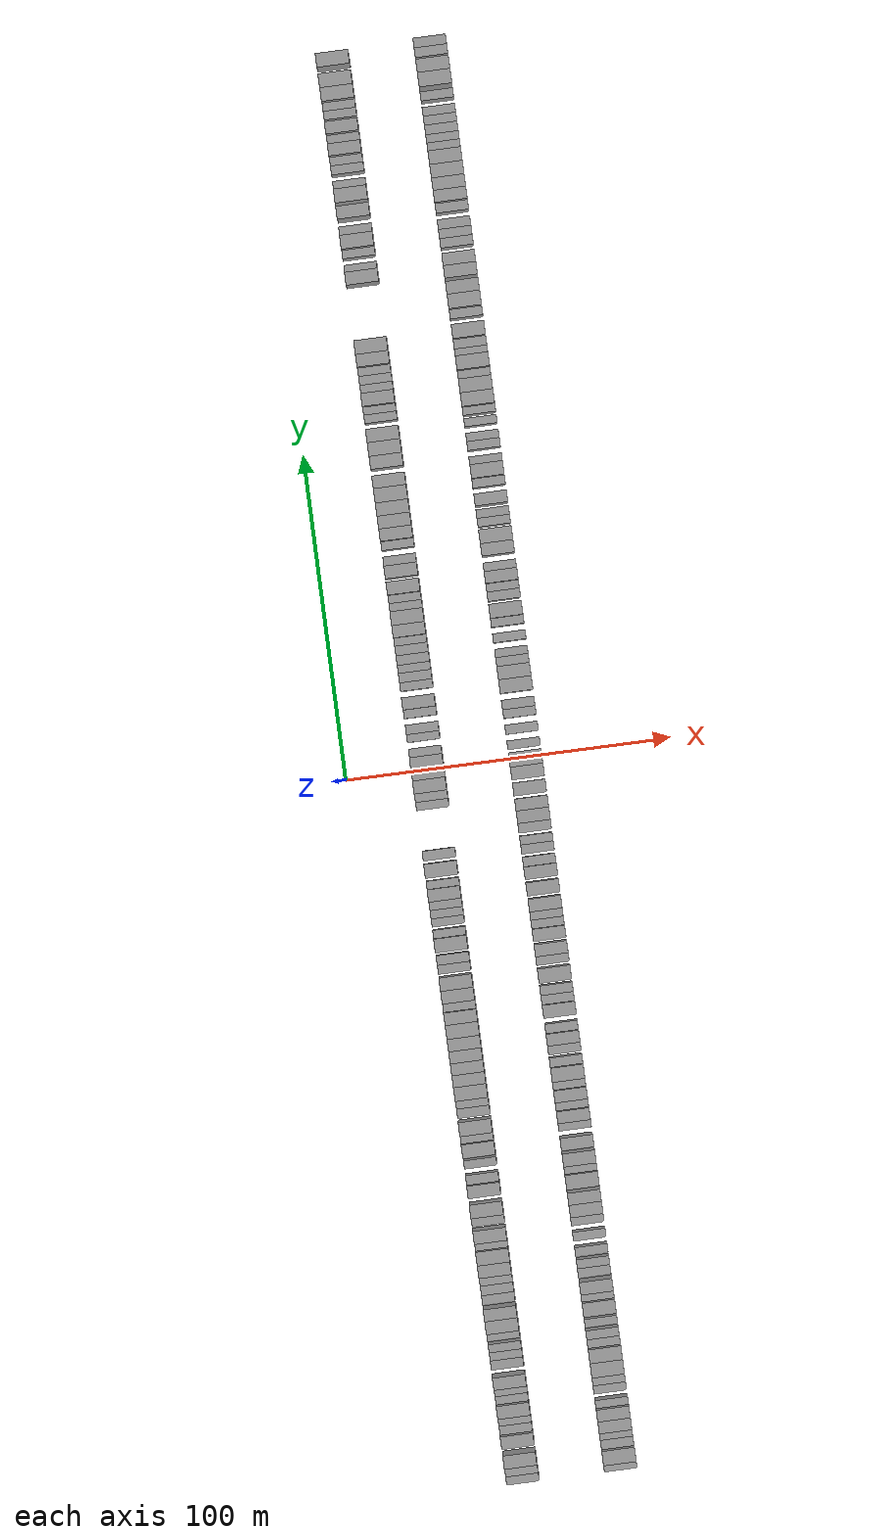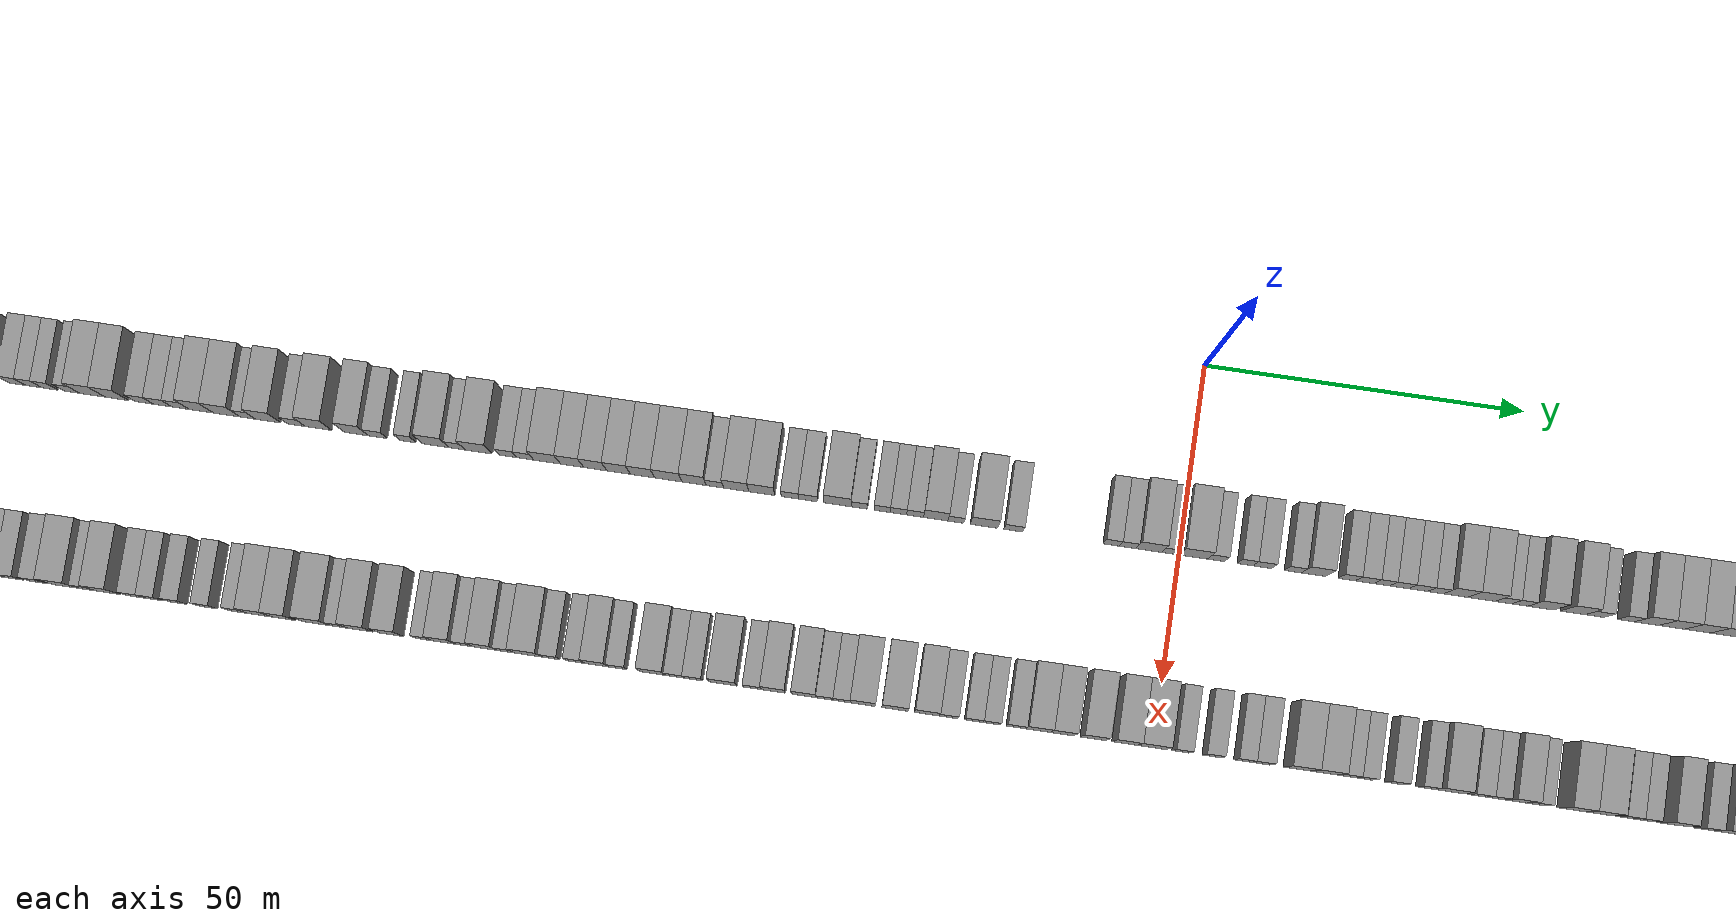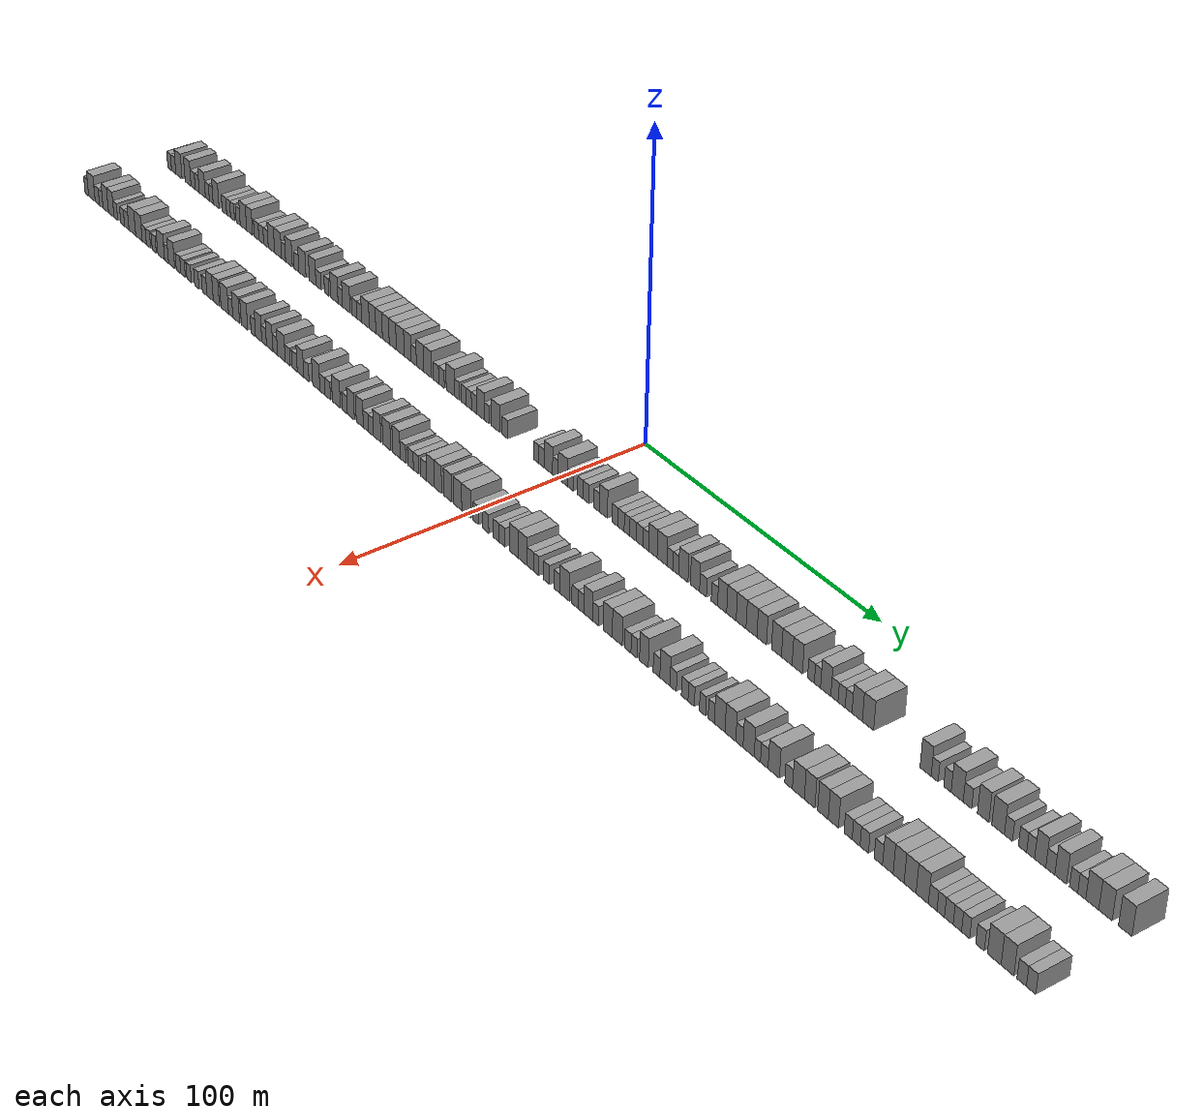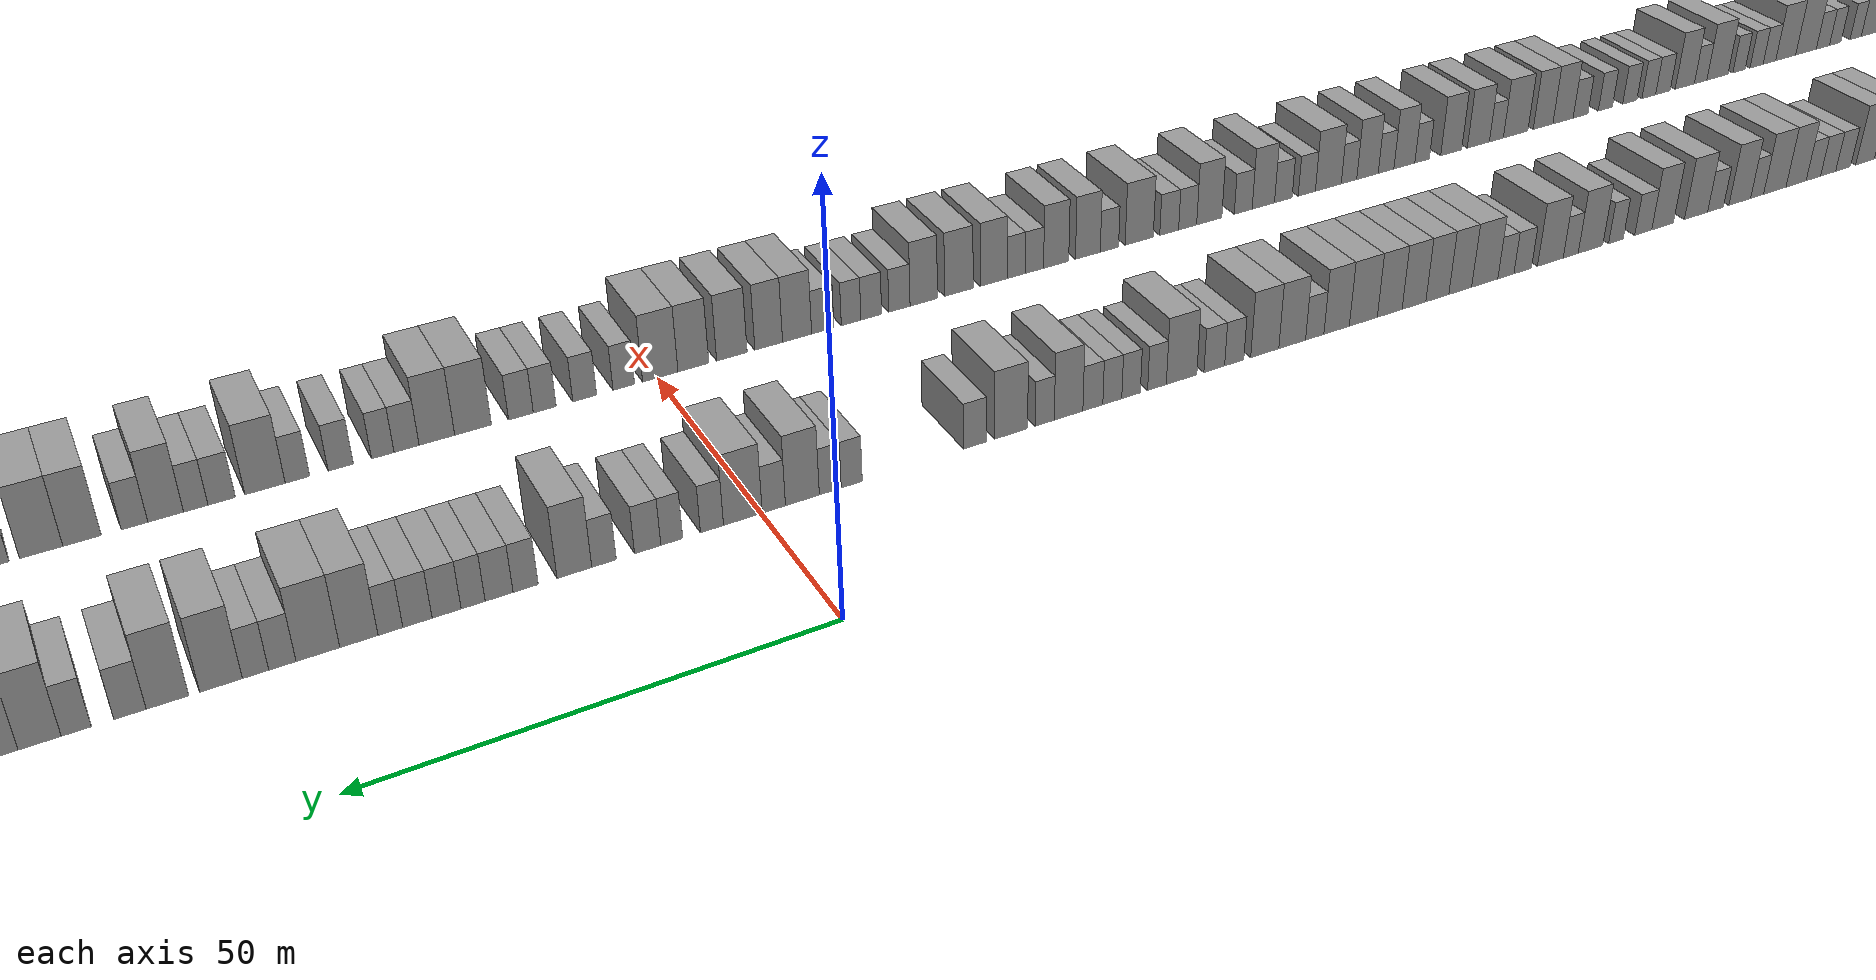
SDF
<sdf version="1.6">
 <world name="default">
  <scene>
   <sky><clouds><speed>12</speed></clouds></sky>
   <ambient>0.4 0.4 0.4 1</ambient>
   <background>0.7 0.7 0.7 1</background>
   <shadows>1</shadows>
  </scene>
  <gravity>0 0 -9.8066</gravity>
  <magnetic_field>6e-06 2.3e-05 -4.2e-05</magnetic_field>
  <physics default="0" name="default_physics" type="ode">
   <ode>
    <solver>
     <type>quick</type>
     <iters>10</iters>
     <sor>1.0</sor>
     <use_dynamic_moi_rescaling>0</use_dynamic_moi_rescaling>
    </solver>
    <constraints>
     <cfm>0</cfm>
     <erp>0.2</erp>
     <contact_max_correcting_vel>100</contact_max_correcting_vel>
     <contact_surface_layer>0.001</contact_surface_layer>
    </constraints>
   </ode>
   <max_step_size>0.004</max_step_size>
   <real_time_factor>1</real_time_factor>
   <real_time_update_rate>250</real_time_update_rate>
  </physics>
  <light name="sun" type="directional">
   <pose>0 0 10 0 0 0</pose>
   <diffuse>0.8 0.8 0.8 1</diffuse>
   <specular>0.2 0.2 0.2 1</specular>
   <attenuation>
    <range>1000</range>
    <constant>0.9</constant>
    <linear>0.01</linear>
    <quadratic>0.001</quadratic>
   </attenuation>
   <direction>-0.5 0.1 -0.9</direction>
  </light>
  <model name="building_1">
   <static>1</static>
   <pose>25.0000 -217.7668 0 0.000000 0.000000 0.000000</pose>
   <link name="link">
    <pose>0 0 3.00 0 0 0</pose>
    <collision name="collision"><geometry><box><size>10.0000 2.4664 6.0000</size></box></geometry></collision>
    <visual name="visual">
     <cast_shadows>0</cast_shadows>
     <geometry><box><size>10.0000 2.4664 6.0000</size></box></geometry>
     <material>
      <script>
       <uri>model://grey_wall/materials/scripts</uri>
       <uri>model://grey_wall/materials/textures</uri>
       <name>vrc/grey_wall</name>
      </script>
     </material>
    </visual>
   </link>
  </model>
  <model name="building_2">
   <static>1</static>
   <pose>25.0000 -215.0972 0 0.000000 0.000000 0.000000</pose>
   <link name="link">
    <pose>0 0 3.00 0 0 0</pose>
    <collision name="collision"><geometry><box><size>10.0000 2.8728 6.0000</size></box></geometry></collision>
    <visual name="visual">
     <cast_shadows>0</cast_shadows>
     <geometry><box><size>10.0000 2.8728 6.0000</size></box></geometry>
     <material>
      <script>
       <uri>model://grey_wall/materials/scripts</uri>
       <uri>model://grey_wall/materials/textures</uri>
       <name>vrc/grey_wall</name>
      </script>
     </material>
    </visual>
   </link>
  </model>
  <model name="building_3">
   <static>1</static>
   <pose>25.0000 -211.6260 0 0.000000 0.000000 0.000000</pose>
   <link name="link">
    <pose>0 0 4.50 0 0 0</pose>
    <collision name="collision"><geometry><box><size>10.0000 4.0696 9.0000</size></box></geometry></collision>
    <visual name="visual">
     <cast_shadows>0</cast_shadows>
     <geometry><box><size>10.0000 4.0696 9.0000</size></box></geometry>
     <material>
      <script>
       <uri>model://grey_wall/materials/scripts</uri>
       <uri>model://grey_wall/materials/textures</uri>
       <name>vrc/grey_wall</name>
      </script>
     </material>
    </visual>
   </link>
  </model>
  <model name="building_4">
   <static>1</static>
   <pose>25.0000 -205.6679 0 0.000000 0.000000 0.000000</pose>
   <link name="link">
    <pose>0 0 4.50 0 0 0</pose>
    <collision name="collision"><geometry><box><size>10.0000 3.8466 9.0000</size></box></geometry></collision>
    <visual name="visual">
     <cast_shadows>0</cast_shadows>
     <geometry><box><size>10.0000 3.8466 9.0000</size></box></geometry>
     <material>
      <script>
       <uri>model://grey_wall/materials/scripts</uri>
       <uri>model://grey_wall/materials/textures</uri>
       <name>vrc/grey_wall</name>
      </script>
     </material>
    </visual>
   </link>
  </model>
  <model name="building_5">
   <static>1</static>
   <pose>25.0000 -202.3643 0 0.000000 0.000000 0.000000</pose>
   <link name="link">
    <pose>0 0 3.00 0 0 0</pose>
    <collision name="collision"><geometry><box><size>10.0000 2.7608 6.0000</size></box></geometry></collision>
    <visual name="visual">
     <cast_shadows>0</cast_shadows>
     <geometry><box><size>10.0000 2.7608 6.0000</size></box></geometry>
     <material>
      <script>
       <uri>model://grey_wall/materials/scripts</uri>
       <uri>model://grey_wall/materials/textures</uri>
       <name>vrc/grey_wall</name>
      </script>
     </material>
    </visual>
   </link>
  </model>
  <model name="building_6">
   <static>1</static>
   <pose>25.0000 -199.6821 0 0.000000 0.000000 0.000000</pose>
   <link name="link">
    <pose>0 0 3.00 0 0 0</pose>
    <collision name="collision"><geometry><box><size>10.0000 2.6036 6.0000</size></box></geometry></collision>
    <visual name="visual">
     <cast_shadows>0</cast_shadows>
     <geometry><box><size>10.0000 2.6036 6.0000</size></box></geometry>
     <material>
      <script>
       <uri>model://grey_wall/materials/scripts</uri>
       <uri>model://grey_wall/materials/textures</uri>
       <name>vrc/grey_wall</name>
      </script>
     </material>
    </visual>
   </link>
  </model>
  <model name="building_7">
   <static>1</static>
   <pose>25.0000 -196.3961 0 0.000000 0.000000 0.000000</pose>
   <link name="link">
    <pose>0 0 4.50 0 0 0</pose>
    <collision name="collision"><geometry><box><size>10.0000 3.9684 9.0000</size></box></geometry></collision>
    <visual name="visual">
     <cast_shadows>0</cast_shadows>
     <geometry><box><size>10.0000 3.9684 9.0000</size></box></geometry>
     <material>
      <script>
       <uri>model://grey_wall/materials/scripts</uri>
       <uri>model://grey_wall/materials/textures</uri>
       <name>vrc/grey_wall</name>
      </script>
     </material>
    </visual>
   </link>
  </model>
  <model name="building_8">
   <static>1</static>
   <pose>25.0000 -193.1541 0 0.000000 0.000000 0.000000</pose>
   <link name="link">
    <pose>0 0 3.00 0 0 0</pose>
    <collision name="collision"><geometry><box><size>10.0000 2.5155 6.0000</size></box></geometry></collision>
    <visual name="visual">
     <cast_shadows>0</cast_shadows>
     <geometry><box><size>10.0000 2.5155 6.0000</size></box></geometry>
     <material>
      <script>
       <uri>model://grey_wall/materials/scripts</uri>
       <uri>model://grey_wall/materials/textures</uri>
       <name>vrc/grey_wall</name>
      </script>
     </material>
    </visual>
   </link>
  </model>
  <model name="building_9">
   <static>1</static>
   <pose>25.0000 -190.6911 0 0.000000 0.000000 0.000000</pose>
   <link name="link">
    <pose>0 0 3.00 0 0 0</pose>
    <collision name="collision"><geometry><box><size>10.0000 2.4105 6.0000</size></box></geometry></collision>
    <visual name="visual">
     <cast_shadows>0</cast_shadows>
     <geometry><box><size>10.0000 2.4105 6.0000</size></box></geometry>
     <material>
      <script>
       <uri>model://grey_wall/materials/scripts</uri>
       <uri>model://grey_wall/materials/textures</uri>
       <name>vrc/grey_wall</name>
      </script>
     </material>
    </visual>
   </link>
  </model>
  <model name="building_10">
   <static>1</static>
   <pose>25.0000 -187.6172 0 0.000000 0.000000 0.000000</pose>
   <link name="link">
    <pose>0 0 4.50 0 0 0</pose>
    <collision name="collision"><geometry><box><size>10.0000 3.7372 9.0000</size></box></geometry></collision>
    <visual name="visual">
     <cast_shadows>0</cast_shadows>
     <geometry><box><size>10.0000 3.7372 9.0000</size></box></geometry>
     <material>
      <script>
       <uri>model://grey_wall/materials/scripts</uri>
       <uri>model://grey_wall/materials/textures</uri>
       <name>vrc/grey_wall</name>
      </script>
     </material>
    </visual>
   </link>
  </model>
  <model name="building_11">
   <static>1</static>
   <pose>25.0000 -182.3425 0 0.000000 0.000000 0.000000</pose>
   <link name="link">
    <pose>0 0 3.00 0 0 0</pose>
    <collision name="collision"><geometry><box><size>10.0000 2.8122 6.0000</size></box></geometry></collision>
    <visual name="visual">
     <cast_shadows>0</cast_shadows>
     <geometry><box><size>10.0000 2.8122 6.0000</size></box></geometry>
     <material>
      <script>
       <uri>model://grey_wall/materials/scripts</uri>
       <uri>model://grey_wall/materials/textures</uri>
       <name>vrc/grey_wall</name>
      </script>
     </material>
    </visual>
   </link>
  </model>
  <model name="building_12">
   <static>1</static>
   <pose>25.0000 -179.6829 0 0.000000 0.000000 0.000000</pose>
   <link name="link">
    <pose>0 0 3.00 0 0 0</pose>
    <collision name="collision"><geometry><box><size>10.0000 2.5071 6.0000</size></box></geometry></collision>
    <visual name="visual">
     <cast_shadows>0</cast_shadows>
     <geometry><box><size>10.0000 2.5071 6.0000</size></box></geometry>
     <material>
      <script>
       <uri>model://grey_wall/materials/scripts</uri>
       <uri>model://grey_wall/materials/textures</uri>
       <name>vrc/grey_wall</name>
      </script>
     </material>
    </visual>
   </link>
  </model>
  <model name="building_13">
   <static>1</static>
   <pose>25.0000 -177.1810 0 0.000000 0.000000 0.000000</pose>
   <link name="link">
    <pose>0 0 3.00 0 0 0</pose>
    <collision name="collision"><geometry><box><size>10.0000 2.4967 6.0000</size></box></geometry></collision>
    <visual name="visual">
     <cast_shadows>0</cast_shadows>
     <geometry><box><size>10.0000 2.4967 6.0000</size></box></geometry>
     <material>
      <script>
       <uri>model://grey_wall/materials/scripts</uri>
       <uri>model://grey_wall/materials/textures</uri>
       <name>vrc/grey_wall</name>
      </script>
     </material>
    </visual>
   </link>
  </model>
  <model name="building_14">
   <static>1</static>
   <pose>25.0000 -173.6939 0 0.000000 0.000000 0.000000</pose>
   <link name="link">
    <pose>0 0 3.00 0 0 0</pose>
    <collision name="collision"><geometry><box><size>10.0000 2.4777 6.0000</size></box></geometry></collision>
    <visual name="visual">
     <cast_shadows>0</cast_shadows>
     <geometry><box><size>10.0000 2.4777 6.0000</size></box></geometry>
     <material>
      <script>
       <uri>model://grey_wall/materials/scripts</uri>
       <uri>model://grey_wall/materials/textures</uri>
       <name>vrc/grey_wall</name>
      </script>
     </material>
    </visual>
   </link>
  </model>
  <model name="building_15">
   <static>1</static>
   <pose>25.0000 -170.4675 0 0.000000 0.000000 0.000000</pose>
   <link name="link">
    <pose>0 0 4.50 0 0 0</pose>
    <collision name="collision"><geometry><box><size>10.0000 3.9750 9.0000</size></box></geometry></collision>
    <visual name="visual">
     <cast_shadows>0</cast_shadows>
     <geometry><box><size>10.0000 3.9750 9.0000</size></box></geometry>
     <material>
      <script>
       <uri>model://grey_wall/materials/scripts</uri>
       <uri>model://grey_wall/materials/textures</uri>
       <name>vrc/grey_wall</name>
      </script>
     </material>
    </visual>
   </link>
  </model>
  <model name="building_16">
   <static>1</static>
   <pose>25.0000 -166.6328 0 0.000000 0.000000 0.000000</pose>
   <link name="link">
    <pose>0 0 4.50 0 0 0</pose>
    <collision name="collision"><geometry><box><size>10.0000 3.6943 9.0000</size></box></geometry></collision>
    <visual name="visual">
     <cast_shadows>0</cast_shadows>
     <geometry><box><size>10.0000 3.6943 9.0000</size></box></geometry>
     <material>
      <script>
       <uri>model://grey_wall/materials/scripts</uri>
       <uri>model://grey_wall/materials/textures</uri>
       <name>vrc/grey_wall</name>
      </script>
     </material>
    </visual>
   </link>
  </model>
  <model name="building_17">
   <static>1</static>
   <pose>25.0000 -162.3408 0 0.000000 0.000000 0.000000</pose>
   <link name="link">
    <pose>0 0 3.00 0 0 0</pose>
    <collision name="collision"><geometry><box><size>10.0000 2.8897 6.0000</size></box></geometry></collision>
    <visual name="visual">
     <cast_shadows>0</cast_shadows>
     <geometry><box><size>10.0000 2.8897 6.0000</size></box></geometry>
     <material>
      <script>
       <uri>model://grey_wall/materials/scripts</uri>
       <uri>model://grey_wall/materials/textures</uri>
       <name>vrc/grey_wall</name>
      </script>
     </material>
    </visual>
   </link>
  </model>
  <model name="building_18">
   <static>1</static>
   <pose>25.0000 -159.4392 0 0.000000 0.000000 0.000000</pose>
   <link name="link">
    <pose>0 0 3.00 0 0 0</pose>
    <collision name="collision"><geometry><box><size>10.0000 2.9136 6.0000</size></box></geometry></collision>
    <visual name="visual">
     <cast_shadows>0</cast_shadows>
     <geometry><box><size>10.0000 2.9136 6.0000</size></box></geometry>
     <material>
      <script>
       <uri>model://grey_wall/materials/scripts</uri>
       <uri>model://grey_wall/materials/textures</uri>
       <name>vrc/grey_wall</name>
      </script>
     </material>
    </visual>
   </link>
  </model>
  <model name="building_19">
   <static>1</static>
   <pose>25.0000 -156.6017 0 0.000000 0.000000 0.000000</pose>
   <link name="link">
    <pose>0 0 3.00 0 0 0</pose>
    <collision name="collision"><geometry><box><size>10.0000 2.7614 6.0000</size></box></geometry></collision>
    <visual name="visual">
     <cast_shadows>0</cast_shadows>
     <geometry><box><size>10.0000 2.7614 6.0000</size></box></geometry>
     <material>
      <script>
       <uri>model://grey_wall/materials/scripts</uri>
       <uri>model://grey_wall/materials/textures</uri>
       <name>vrc/grey_wall</name>
      </script>
     </material>
    </visual>
   </link>
  </model>
  <model name="building_20">
   <static>1</static>
   <pose>25.0000 -153.3091 0 0.000000 0.000000 0.000000</pose>
   <link name="link">
    <pose>0 0 4.50 0 0 0</pose>
    <collision name="collision"><geometry><box><size>10.0000 3.8238 9.0000</size></box></geometry></collision>
    <visual name="visual">
     <cast_shadows>0</cast_shadows>
     <geometry><box><size>10.0000 3.8238 9.0000</size></box></geometry>
     <material>
      <script>
       <uri>model://grey_wall/materials/scripts</uri>
       <uri>model://grey_wall/materials/textures</uri>
       <name>vrc/grey_wall</name>
      </script>
     </material>
    </visual>
   </link>
  </model>
  <model name="building_21">
   <static>1</static>
   <pose>25.0000 -149.2970 0 0.000000 0.000000 0.000000</pose>
   <link name="link">
    <pose>0 0 4.50 0 0 0</pose>
    <collision name="collision"><geometry><box><size>10.0000 4.2003 9.0000</size></box></geometry></collision>
    <visual name="visual">
     <cast_shadows>0</cast_shadows>
     <geometry><box><size>10.0000 4.2003 9.0000</size></box></geometry>
     <material>
      <script>
       <uri>model://grey_wall/materials/scripts</uri>
       <uri>model://grey_wall/materials/textures</uri>
       <name>vrc/grey_wall</name>
      </script>
     </material>
    </visual>
   </link>
  </model>
  <model name="building_22">
   <static>1</static>
   <pose>25.0000 -145.9917 0 0.000000 0.000000 0.000000</pose>
   <link name="link">
    <pose>0 0 3.00 0 0 0</pose>
    <collision name="collision"><geometry><box><size>10.0000 2.4105 6.0000</size></box></geometry></collision>
    <visual name="visual">
     <cast_shadows>0</cast_shadows>
     <geometry><box><size>10.0000 2.4105 6.0000</size></box></geometry>
     <material>
      <script>
       <uri>model://grey_wall/materials/scripts</uri>
       <uri>model://grey_wall/materials/textures</uri>
       <name>vrc/grey_wall</name>
      </script>
     </material>
    </visual>
   </link>
  </model>
  <model name="building_23">
   <static>1</static>
   <pose>25.0000 -142.7866 0 0.000000 0.000000 0.000000</pose>
   <link name="link">
    <pose>0 0 4.50 0 0 0</pose>
    <collision name="collision"><geometry><box><size>10.0000 3.9996 9.0000</size></box></geometry></collision>
    <visual name="visual">
     <cast_shadows>0</cast_shadows>
     <geometry><box><size>10.0000 3.9996 9.0000</size></box></geometry>
     <material>
      <script>
       <uri>model://grey_wall/materials/scripts</uri>
       <uri>model://grey_wall/materials/textures</uri>
       <name>vrc/grey_wall</name>
      </script>
     </material>
    </visual>
   </link>
  </model>
  <model name="building_24">
   <static>1</static>
   <pose>25.0000 -138.3526 0 0.000000 0.000000 0.000000</pose>
   <link name="link">
    <pose>0 0 3.00 0 0 0</pose>
    <collision name="collision"><geometry><box><size>10.0000 2.8685 6.0000</size></box></geometry></collision>
    <visual name="visual">
     <cast_shadows>0</cast_shadows>
     <geometry><box><size>10.0000 2.8685 6.0000</size></box></geometry>
     <material>
      <script>
       <uri>model://grey_wall/materials/scripts</uri>
       <uri>model://grey_wall/materials/textures</uri>
       <name>vrc/grey_wall</name>
      </script>
     </material>
    </visual>
   </link>
  </model>
  <model name="building_25">
   <static>1</static>
   <pose>25.0000 -134.8395 0 0.000000 0.000000 0.000000</pose>
   <link name="link">
    <pose>0 0 4.50 0 0 0</pose>
    <collision name="collision"><geometry><box><size>10.0000 4.1577 9.0000</size></box></geometry></collision>
    <visual name="visual">
     <cast_shadows>0</cast_shadows>
     <geometry><box><size>10.0000 4.1577 9.0000</size></box></geometry>
     <material>
      <script>
       <uri>model://grey_wall/materials/scripts</uri>
       <uri>model://grey_wall/materials/textures</uri>
       <name>vrc/grey_wall</name>
      </script>
     </material>
    </visual>
   </link>
  </model>
  <model name="building_26">
   <static>1</static>
   <pose>25.0000 -128.8583 0 0.000000 0.000000 0.000000</pose>
   <link name="link">
    <pose>0 0 4.50 0 0 0</pose>
    <collision name="collision"><geometry><box><size>10.0000 3.8046 9.0000</size></box></geometry></collision>
    <visual name="visual">
     <cast_shadows>0</cast_shadows>
     <geometry><box><size>10.0000 3.8046 9.0000</size></box></geometry>
     <material>
      <script>
       <uri>model://grey_wall/materials/scripts</uri>
       <uri>model://grey_wall/materials/textures</uri>
       <name>vrc/grey_wall</name>
      </script>
     </material>
    </visual>
   </link>
  </model>
  <model name="building_27">
   <static>1</static>
   <pose>25.0000 -125.4701 0 0.000000 0.000000 0.000000</pose>
   <link name="link">
    <pose>0 0 3.00 0 0 0</pose>
    <collision name="collision"><geometry><box><size>10.0000 2.9719 6.0000</size></box></geometry></collision>
    <visual name="visual">
     <cast_shadows>0</cast_shadows>
     <geometry><box><size>10.0000 2.9719 6.0000</size></box></geometry>
     <material>
      <script>
       <uri>model://grey_wall/materials/scripts</uri>
       <uri>model://grey_wall/materials/textures</uri>
       <name>vrc/grey_wall</name>
      </script>
     </material>
    </visual>
   </link>
  </model>
  <model name="building_28">
   <static>1</static>
   <pose>25.0000 -120.7214 0 0.000000 0.000000 0.000000</pose>
   <link name="link">
    <pose>0 0 3.00 0 0 0</pose>
    <collision name="collision"><geometry><box><size>10.0000 2.5256 6.0000</size></box></geometry></collision>
    <visual name="visual">
     <cast_shadows>0</cast_shadows>
     <geometry><box><size>10.0000 2.5256 6.0000</size></box></geometry>
     <material>
      <script>
       <uri>model://grey_wall/materials/scripts</uri>
       <uri>model://grey_wall/materials/textures</uri>
       <name>vrc/grey_wall</name>
      </script>
     </material>
    </visual>
   </link>
  </model>
  <model name="building_29">
   <static>1</static>
   <pose>25.0000 -116.3703 0 0.000000 0.000000 0.000000</pose>
   <link name="link">
    <pose>0 0 4.50 0 0 0</pose>
    <collision name="collision"><geometry><box><size>10.0000 4.1766 9.0000</size></box></geometry></collision>
    <visual name="visual">
     <cast_shadows>0</cast_shadows>
     <geometry><box><size>10.0000 4.1766 9.0000</size></box></geometry>
     <material>
      <script>
       <uri>model://grey_wall/materials/scripts</uri>
       <uri>model://grey_wall/materials/textures</uri>
       <name>vrc/grey_wall</name>
      </script>
     </material>
    </visual>
   </link>
  </model>
  <model name="building_30">
   <static>1</static>
   <pose>25.0000 -113.0198 0 0.000000 0.000000 0.000000</pose>
   <link name="link">
    <pose>0 0 3.00 0 0 0</pose>
    <collision name="collision"><geometry><box><size>10.0000 2.5243 6.0000</size></box></geometry></collision>
    <visual name="visual">
     <cast_shadows>0</cast_shadows>
     <geometry><box><size>10.0000 2.5243 6.0000</size></box></geometry>
     <material>
      <script>
       <uri>model://grey_wall/materials/scripts</uri>
       <uri>model://grey_wall/materials/textures</uri>
       <name>vrc/grey_wall</name>
      </script>
     </material>
    </visual>
   </link>
  </model>
  <model name="building_31">
   <static>1</static>
   <pose>25.0000 -109.6110 0 0.000000 0.000000 0.000000</pose>
   <link name="link">
    <pose>0 0 4.50 0 0 0</pose>
    <collision name="collision"><geometry><box><size>10.0000 4.2934 9.0000</size></box></geometry></collision>
    <visual name="visual">
     <cast_shadows>0</cast_shadows>
     <geometry><box><size>10.0000 4.2934 9.0000</size></box></geometry>
     <material>
      <script>
       <uri>model://grey_wall/materials/scripts</uri>
       <uri>model://grey_wall/materials/textures</uri>
       <name>vrc/grey_wall</name>
      </script>
     </material>
    </visual>
   </link>
  </model>
  <model name="building_32">
   <static>1</static>
   <pose>25.0000 -105.0264 0 0.000000 0.000000 0.000000</pose>
   <link name="link">
    <pose>0 0 3.00 0 0 0</pose>
    <collision name="collision"><geometry><box><size>10.0000 2.8757 6.0000</size></box></geometry></collision>
    <visual name="visual">
     <cast_shadows>0</cast_shadows>
     <geometry><box><size>10.0000 2.8757 6.0000</size></box></geometry>
     <material>
      <script>
       <uri>model://grey_wall/materials/scripts</uri>
       <uri>model://grey_wall/materials/textures</uri>
       <name>vrc/grey_wall</name>
      </script>
     </material>
    </visual>
   </link>
  </model>
  <model name="building_33">
   <static>1</static>
   <pose>25.0000 -102.2784 0 0.000000 0.000000 0.000000</pose>
   <link name="link">
    <pose>0 0 3.00 0 0 0</pose>
    <collision name="collision"><geometry><box><size>10.0000 2.6205 6.0000</size></box></geometry></collision>
    <visual name="visual">
     <cast_shadows>0</cast_shadows>
     <geometry><box><size>10.0000 2.6205 6.0000</size></box></geometry>
     <material>
      <script>
       <uri>model://grey_wall/materials/scripts</uri>
       <uri>model://grey_wall/materials/textures</uri>
       <name>vrc/grey_wall</name>
      </script>
     </material>
    </visual>
   </link>
  </model>
  <model name="building_34">
   <static>1</static>
   <pose>25.0000 -98.8561 0 0.000000 0.000000 0.000000</pose>
   <link name="link">
    <pose>0 0 4.50 0 0 0</pose>
    <collision name="collision"><geometry><box><size>10.0000 4.2241 9.0000</size></box></geometry></collision>
    <visual name="visual">
     <cast_shadows>0</cast_shadows>
     <geometry><box><size>10.0000 4.2241 9.0000</size></box></geometry>
     <material>
      <script>
       <uri>model://grey_wall/materials/scripts</uri>
       <uri>model://grey_wall/materials/textures</uri>
       <name>vrc/grey_wall</name>
      </script>
     </material>
    </visual>
   </link>
  </model>
  <model name="building_35">
   <static>1</static>
   <pose>25.0000 -94.9230 0 0.000000 0.000000 0.000000</pose>
   <link name="link">
    <pose>0 0 4.50 0 0 0</pose>
    <collision name="collision"><geometry><box><size>10.0000 3.6422 9.0000</size></box></geometry></collision>
    <visual name="visual">
     <cast_shadows>0</cast_shadows>
     <geometry><box><size>10.0000 3.6422 9.0000</size></box></geometry>
     <material>
      <script>
       <uri>model://grey_wall/materials/scripts</uri>
       <uri>model://grey_wall/materials/textures</uri>
       <name>vrc/grey_wall</name>
      </script>
     </material>
    </visual>
   </link>
  </model>
  <model name="building_36">
   <static>1</static>
   <pose>25.0000 -91.2906 0 0.000000 0.000000 0.000000</pose>
   <link name="link">
    <pose>0 0 4.50 0 0 0</pose>
    <collision name="collision"><geometry><box><size>10.0000 3.6224 9.0000</size></box></geometry></collision>
    <visual name="visual">
     <cast_shadows>0</cast_shadows>
     <geometry><box><size>10.0000 3.6224 9.0000</size></box></geometry>
     <material>
      <script>
       <uri>model://grey_wall/materials/scripts</uri>
       <uri>model://grey_wall/materials/textures</uri>
       <name>vrc/grey_wall</name>
      </script>
     </material>
    </visual>
   </link>
  </model>
  <model name="building_37">
   <static>1</static>
   <pose>25.0000 -87.6306 0 0.000000 0.000000 0.000000</pose>
   <link name="link">
    <pose>0 0 4.50 0 0 0</pose>
    <collision name="collision"><geometry><box><size>10.0000 3.6977 9.0000</size></box></geometry></collision>
    <visual name="visual">
     <cast_shadows>0</cast_shadows>
     <geometry><box><size>10.0000 3.6977 9.0000</size></box></geometry>
     <material>
      <script>
       <uri>model://grey_wall/materials/scripts</uri>
       <uri>model://grey_wall/materials/textures</uri>
       <name>vrc/grey_wall</name>
      </script>
     </material>
    </visual>
   </link>
  </model>
  <model name="building_38">
   <static>1</static>
   <pose>25.0000 -83.8737 0 0.000000 0.000000 0.000000</pose>
   <link name="link">
    <pose>0 0 4.50 0 0 0</pose>
    <collision name="collision"><geometry><box><size>10.0000 3.8162 9.0000</size></box></geometry></collision>
    <visual name="visual">
     <cast_shadows>0</cast_shadows>
     <geometry><box><size>10.0000 3.8162 9.0000</size></box></geometry>
     <material>
      <script>
       <uri>model://grey_wall/materials/scripts</uri>
       <uri>model://grey_wall/materials/textures</uri>
       <name>vrc/grey_wall</name>
      </script>
     </material>
    </visual>
   </link>
  </model>
  <model name="building_39">
   <static>1</static>
   <pose>25.0000 -79.8392 0 0.000000 0.000000 0.000000</pose>
   <link name="link">
    <pose>0 0 4.50 0 0 0</pose>
    <collision name="collision"><geometry><box><size>10.0000 4.2527 9.0000</size></box></geometry></collision>
    <visual name="visual">
     <cast_shadows>0</cast_shadows>
     <geometry><box><size>10.0000 4.2527 9.0000</size></box></geometry>
     <material>
      <script>
       <uri>model://grey_wall/materials/scripts</uri>
       <uri>model://grey_wall/materials/textures</uri>
       <name>vrc/grey_wall</name>
      </script>
     </material>
    </visual>
   </link>
  </model>
  <model name="building_40">
   <static>1</static>
   <pose>25.0000 -75.8029 0 0.000000 0.000000 0.000000</pose>
   <link name="link">
    <pose>0 0 4.50 0 0 0</pose>
    <collision name="collision"><geometry><box><size>10.0000 3.8200 9.0000</size></box></geometry></collision>
    <visual name="visual">
     <cast_shadows>0</cast_shadows>
     <geometry><box><size>10.0000 3.8200 9.0000</size></box></geometry>
     <material>
      <script>
       <uri>model://grey_wall/materials/scripts</uri>
       <uri>model://grey_wall/materials/textures</uri>
       <name>vrc/grey_wall</name>
      </script>
     </material>
    </visual>
   </link>
  </model>
  <model name="building_41">
   <static>1</static>
   <pose>25.0000 -72.5315 0 0.000000 0.000000 0.000000</pose>
   <link name="link">
    <pose>0 0 3.00 0 0 0</pose>
    <collision name="collision"><geometry><box><size>10.0000 2.7228 6.0000</size></box></geometry></collision>
    <visual name="visual">
     <cast_shadows>0</cast_shadows>
     <geometry><box><size>10.0000 2.7228 6.0000</size></box></geometry>
     <material>
      <script>
       <uri>model://grey_wall/materials/scripts</uri>
       <uri>model://grey_wall/materials/textures</uri>
       <name>vrc/grey_wall</name>
      </script>
     </material>
    </visual>
   </link>
  </model>
  <model name="building_42">
   <static>1</static>
   <pose>25.0000 -69.2048 0 0.000000 0.000000 0.000000</pose>
   <link name="link">
    <pose>0 0 4.50 0 0 0</pose>
    <collision name="collision"><geometry><box><size>10.0000 3.9304 9.0000</size></box></geometry></collision>
    <visual name="visual">
     <cast_shadows>0</cast_shadows>
     <geometry><box><size>10.0000 3.9304 9.0000</size></box></geometry>
     <material>
      <script>
       <uri>model://grey_wall/materials/scripts</uri>
       <uri>model://grey_wall/materials/textures</uri>
       <name>vrc/grey_wall</name>
      </script>
     </material>
    </visual>
   </link>
  </model>
  <model name="building_43">
   <static>1</static>
   <pose>25.0000 -65.2022 0 0.000000 0.000000 0.000000</pose>
   <link name="link">
    <pose>0 0 4.50 0 0 0</pose>
    <collision name="collision"><geometry><box><size>10.0000 4.0749 9.0000</size></box></geometry></collision>
    <visual name="visual">
     <cast_shadows>0</cast_shadows>
     <geometry><box><size>10.0000 4.0749 9.0000</size></box></geometry>
     <material>
      <script>
       <uri>model://grey_wall/materials/scripts</uri>
       <uri>model://grey_wall/materials/textures</uri>
       <name>vrc/grey_wall</name>
      </script>
     </material>
    </visual>
   </link>
  </model>
  <model name="building_44">
   <static>1</static>
   <pose>25.0000 -60.7975 0 0.000000 0.000000 0.000000</pose>
   <link name="link">
    <pose>0 0 3.00 0 0 0</pose>
    <collision name="collision"><geometry><box><size>10.0000 2.7345 6.0000</size></box></geometry></collision>
    <visual name="visual">
     <cast_shadows>0</cast_shadows>
     <geometry><box><size>10.0000 2.7345 6.0000</size></box></geometry>
     <material>
      <script>
       <uri>model://grey_wall/materials/scripts</uri>
       <uri>model://grey_wall/materials/textures</uri>
       <name>vrc/grey_wall</name>
      </script>
     </material>
    </visual>
   </link>
  </model>
  <model name="building_45">
   <static>1</static>
   <pose>25.0000 -57.9662 0 0.000000 0.000000 0.000000</pose>
   <link name="link">
    <pose>0 0 3.00 0 0 0</pose>
    <collision name="collision"><geometry><box><size>10.0000 2.9279 6.0000</size></box></geometry></collision>
    <visual name="visual">
     <cast_shadows>0</cast_shadows>
     <geometry><box><size>10.0000 2.9279 6.0000</size></box></geometry>
     <material>
      <script>
       <uri>model://grey_wall/materials/scripts</uri>
       <uri>model://grey_wall/materials/textures</uri>
       <name>vrc/grey_wall</name>
      </script>
     </material>
    </visual>
   </link>
  </model>
  <model name="building_46">
   <static>1</static>
   <pose>25.0000 -53.3754 0 0.000000 0.000000 0.000000</pose>
   <link name="link">
    <pose>0 0 4.50 0 0 0</pose>
    <collision name="collision"><geometry><box><size>10.0000 4.2537 9.0000</size></box></geometry></collision>
    <visual name="visual">
     <cast_shadows>0</cast_shadows>
     <geometry><box><size>10.0000 4.2537 9.0000</size></box></geometry>
     <material>
      <script>
       <uri>model://grey_wall/materials/scripts</uri>
       <uri>model://grey_wall/materials/textures</uri>
       <name>vrc/grey_wall</name>
      </script>
     </material>
    </visual>
   </link>
  </model>
  <model name="building_47">
   <static>1</static>
   <pose>25.0000 -49.9605 0 0.000000 0.000000 0.000000</pose>
   <link name="link">
    <pose>0 0 3.00 0 0 0</pose>
    <collision name="collision"><geometry><box><size>10.0000 2.5762 6.0000</size></box></geometry></collision>
    <visual name="visual">
     <cast_shadows>0</cast_shadows>
     <geometry><box><size>10.0000 2.5762 6.0000</size></box></geometry>
     <material>
      <script>
       <uri>model://grey_wall/materials/scripts</uri>
       <uri>model://grey_wall/materials/textures</uri>
       <name>vrc/grey_wall</name>
      </script>
     </material>
    </visual>
   </link>
  </model>
  <model name="building_48">
   <static>1</static>
   <pose>25.0000 -46.4089 0 0.000000 0.000000 0.000000</pose>
   <link name="link">
    <pose>0 0 3.00 0 0 0</pose>
    <collision name="collision"><geometry><box><size>10.0000 2.5269 6.0000</size></box></geometry></collision>
    <visual name="visual">
     <cast_shadows>0</cast_shadows>
     <geometry><box><size>10.0000 2.5269 6.0000</size></box></geometry>
     <material>
      <script>
       <uri>model://grey_wall/materials/scripts</uri>
       <uri>model://grey_wall/materials/textures</uri>
       <name>vrc/grey_wall</name>
      </script>
     </material>
    </visual>
   </link>
  </model>
  <model name="building_49">
   <static>1</static>
   <pose>25.0000 -43.8658 0 0.000000 0.000000 0.000000</pose>
   <link name="link">
    <pose>0 0 3.00 0 0 0</pose>
    <collision name="collision"><geometry><box><size>10.0000 2.5592 6.0000</size></box></geometry></collision>
    <visual name="visual">
     <cast_shadows>0</cast_shadows>
     <geometry><box><size>10.0000 2.5592 6.0000</size></box></geometry>
     <material>
      <script>
       <uri>model://grey_wall/materials/scripts</uri>
       <uri>model://grey_wall/materials/textures</uri>
       <name>vrc/grey_wall</name>
      </script>
     </material>
    </visual>
   </link>
  </model>
  <model name="building_50">
   <static>1</static>
   <pose>25.0000 -41.2509 0 0.000000 0.000000 0.000000</pose>
   <link name="link">
    <pose>0 0 3.00 0 0 0</pose>
    <collision name="collision"><geometry><box><size>10.0000 2.6707 6.0000</size></box></geometry></collision>
    <visual name="visual">
     <cast_shadows>0</cast_shadows>
     <geometry><box><size>10.0000 2.6707 6.0000</size></box></geometry>
     <material>
      <script>
       <uri>model://grey_wall/materials/scripts</uri>
       <uri>model://grey_wall/materials/textures</uri>
       <name>vrc/grey_wall</name>
      </script>
     </material>
    </visual>
   </link>
  </model>
  <model name="building_51">
   <static>1</static>
   <pose>25.0000 -38.0230 0 0.000000 0.000000 0.000000</pose>
   <link name="link">
    <pose>0 0 4.50 0 0 0</pose>
    <collision name="collision"><geometry><box><size>10.0000 3.7851 9.0000</size></box></geometry></collision>
    <visual name="visual">
     <cast_shadows>0</cast_shadows>
     <geometry><box><size>10.0000 3.7851 9.0000</size></box></geometry>
     <material>
      <script>
       <uri>model://grey_wall/materials/scripts</uri>
       <uri>model://grey_wall/materials/textures</uri>
       <name>vrc/grey_wall</name>
      </script>
     </material>
    </visual>
   </link>
  </model>
  <model name="building_52">
   <static>1</static>
   <pose>25.0000 -34.8831 0 0.000000 0.000000 0.000000</pose>
   <link name="link">
    <pose>0 0 3.00 0 0 0</pose>
    <collision name="collision"><geometry><box><size>10.0000 2.4947 6.0000</size></box></geometry></collision>
    <visual name="visual">
     <cast_shadows>0</cast_shadows>
     <geometry><box><size>10.0000 2.4947 6.0000</size></box></geometry>
     <material>
      <script>
       <uri>model://grey_wall/materials/scripts</uri>
       <uri>model://grey_wall/materials/textures</uri>
       <name>vrc/grey_wall</name>
      </script>
     </material>
    </visual>
   </link>
  </model>
  <model name="building_53">
   <static>1</static>
   <pose>25.0000 -30.5118 0 0.000000 0.000000 0.000000</pose>
   <link name="link">
    <pose>0 0 4.50 0 0 0</pose>
    <collision name="collision"><geometry><box><size>10.0000 4.2481 9.0000</size></box></geometry></collision>
    <visual name="visual">
     <cast_shadows>0</cast_shadows>
     <geometry><box><size>10.0000 4.2481 9.0000</size></box></geometry>
     <material>
      <script>
       <uri>model://grey_wall/materials/scripts</uri>
       <uri>model://grey_wall/materials/textures</uri>
       <name>vrc/grey_wall</name>
      </script>
     </material>
    </visual>
   </link>
  </model>
  <model name="building_54">
   <static>1</static>
   <pose>25.0000 -25.9126 0 0.000000 0.000000 0.000000</pose>
   <link name="link">
    <pose>0 0 3.00 0 0 0</pose>
    <collision name="collision"><geometry><box><size>10.0000 2.9503 6.0000</size></box></geometry></collision>
    <visual name="visual">
     <cast_shadows>0</cast_shadows>
     <geometry><box><size>10.0000 2.9503 6.0000</size></box></geometry>
     <material>
      <script>
       <uri>model://grey_wall/materials/scripts</uri>
       <uri>model://grey_wall/materials/textures</uri>
       <name>vrc/grey_wall</name>
      </script>
     </material>
    </visual>
   </link>
  </model>
  <model name="building_55">
   <static>1</static>
   <pose>25.0000 -10.6494 0 0.000000 0.000000 0.000000</pose>
   <link name="link">
    <pose>0 0 3.00 0 0 0</pose>
    <collision name="collision"><geometry><box><size>10.0000 2.5254 6.0000</size></box></geometry></collision>
    <visual name="visual">
     <cast_shadows>0</cast_shadows>
     <geometry><box><size>10.0000 2.5254 6.0000</size></box></geometry>
     <material>
      <script>
       <uri>model://grey_wall/materials/scripts</uri>
       <uri>model://grey_wall/materials/textures</uri>
       <name>vrc/grey_wall</name>
      </script>
     </material>
    </visual>
   </link>
  </model>
  <model name="building_56">
   <static>1</static>
   <pose>25.0000 -8.0815 0 0.000000 0.000000 0.000000</pose>
   <link name="link">
    <pose>0 0 3.00 0 0 0</pose>
    <collision name="collision"><geometry><box><size>10.0000 2.6104 6.0000</size></box></geometry></collision>
    <visual name="visual">
     <cast_shadows>0</cast_shadows>
     <geometry><box><size>10.0000 2.6104 6.0000</size></box></geometry>
     <material>
      <script>
       <uri>model://grey_wall/materials/scripts</uri>
       <uri>model://grey_wall/materials/textures</uri>
       <name>vrc/grey_wall</name>
      </script>
     </material>
    </visual>
   </link>
  </model>
  <model name="building_57">
   <static>1</static>
   <pose>25.0000 -4.7833 0 0.000000 0.000000 0.000000</pose>
   <link name="link">
    <pose>0 0 4.50 0 0 0</pose>
    <collision name="collision"><geometry><box><size>10.0000 3.9858 9.0000</size></box></geometry></collision>
    <visual name="visual">
     <cast_shadows>0</cast_shadows>
     <geometry><box><size>10.0000 3.9858 9.0000</size></box></geometry>
     <material>
      <script>
       <uri>model://grey_wall/materials/scripts</uri>
       <uri>model://grey_wall/materials/textures</uri>
       <name>vrc/grey_wall</name>
      </script>
     </material>
    </visual>
   </link>
  </model>
  <model name="building_58">
   <static>1</static>
   <pose>25.0000 -1.4398 0 0.000000 0.000000 0.000000</pose>
   <link name="link">
    <pose>0 0 3.00 0 0 0</pose>
    <collision name="collision"><geometry><box><size>10.0000 2.7014 6.0000</size></box></geometry></collision>
    <visual name="visual">
     <cast_shadows>0</cast_shadows>
     <geometry><box><size>10.0000 2.7014 6.0000</size></box></geometry>
     <material>
      <script>
       <uri>model://grey_wall/materials/scripts</uri>
       <uri>model://grey_wall/materials/textures</uri>
       <name>vrc/grey_wall</name>
      </script>
     </material>
    </visual>
   </link>
  </model>
  <model name="building_59">
   <static>1</static>
   <pose>25.0000 2.1377 0 0.000000 0.000000 0.000000</pose>
   <link name="link">
    <pose>0 0 4.50 0 0 0</pose>
    <collision name="collision"><geometry><box><size>10.0000 4.4536 9.0000</size></box></geometry></collision>
    <visual name="visual">
     <cast_shadows>0</cast_shadows>
     <geometry><box><size>10.0000 4.4536 9.0000</size></box></geometry>
     <material>
      <script>
       <uri>model://grey_wall/materials/scripts</uri>
       <uri>model://grey_wall/materials/textures</uri>
       <name>vrc/grey_wall</name>
      </script>
     </material>
    </visual>
   </link>
  </model>
  <model name="building_60">
   <static>1</static>
   <pose>25.0000 5.6719 0 0.000000 0.000000 0.000000</pose>
   <link name="link">
    <pose>0 0 3.00 0 0 0</pose>
    <collision name="collision"><geometry><box><size>10.0000 2.6147 6.0000</size></box></geometry></collision>
    <visual name="visual">
     <cast_shadows>0</cast_shadows>
     <geometry><box><size>10.0000 2.6147 6.0000</size></box></geometry>
     <material>
      <script>
       <uri>model://grey_wall/materials/scripts</uri>
       <uri>model://grey_wall/materials/textures</uri>
       <name>vrc/grey_wall</name>
      </script>
     </material>
    </visual>
   </link>
  </model>
  <model name="building_61">
   <static>1</static>
   <pose>25.0000 10.1976 0 0.000000 0.000000 0.000000</pose>
   <link name="link">
    <pose>0 0 3.00 0 0 0</pose>
    <collision name="collision"><geometry><box><size>10.0000 2.4369 6.0000</size></box></geometry></collision>
    <visual name="visual">
     <cast_shadows>0</cast_shadows>
     <geometry><box><size>10.0000 2.4369 6.0000</size></box></geometry>
     <material>
      <script>
       <uri>model://grey_wall/materials/scripts</uri>
       <uri>model://grey_wall/materials/textures</uri>
       <name>vrc/grey_wall</name>
      </script>
     </material>
    </visual>
   </link>
  </model>
  <model name="building_62">
   <static>1</static>
   <pose>25.0000 12.8672 0 0.000000 0.000000 0.000000</pose>
   <link name="link">
    <pose>0 0 3.00 0 0 0</pose>
    <collision name="collision"><geometry><box><size>10.0000 2.9022 6.0000</size></box></geometry></collision>
    <visual name="visual">
     <cast_shadows>0</cast_shadows>
     <geometry><box><size>10.0000 2.9022 6.0000</size></box></geometry>
     <material>
      <script>
       <uri>model://grey_wall/materials/scripts</uri>
       <uri>model://grey_wall/materials/textures</uri>
       <name>vrc/grey_wall</name>
      </script>
     </material>
    </visual>
   </link>
  </model>
  <model name="building_63">
   <static>1</static>
   <pose>25.0000 17.6423 0 0.000000 0.000000 0.000000</pose>
   <link name="link">
    <pose>0 0 3.00 0 0 0</pose>
    <collision name="collision"><geometry><box><size>10.0000 2.6480 6.0000</size></box></geometry></collision>
    <visual name="visual">
     <cast_shadows>0</cast_shadows>
     <geometry><box><size>10.0000 2.6480 6.0000</size></box></geometry>
     <material>
      <script>
       <uri>model://grey_wall/materials/scripts</uri>
       <uri>model://grey_wall/materials/textures</uri>
       <name>vrc/grey_wall</name>
      </script>
     </material>
    </visual>
   </link>
  </model>
  <model name="building_64">
   <static>1</static>
   <pose>25.0000 20.8289 0 0.000000 0.000000 0.000000</pose>
   <link name="link">
    <pose>0 0 4.50 0 0 0</pose>
    <collision name="collision"><geometry><box><size>10.0000 3.7254 9.0000</size></box></geometry></collision>
    <visual name="visual">
     <cast_shadows>0</cast_shadows>
     <geometry><box><size>10.0000 3.7254 9.0000</size></box></geometry>
     <material>
      <script>
       <uri>model://grey_wall/materials/scripts</uri>
       <uri>model://grey_wall/materials/textures</uri>
       <name>vrc/grey_wall</name>
      </script>
     </material>
    </visual>
   </link>
  </model>
  <model name="building_65">
   <static>1</static>
   <pose>25.0000 26.0097 0 0.000000 0.000000 0.000000</pose>
   <link name="link">
    <pose>0 0 3.00 0 0 0</pose>
    <collision name="collision"><geometry><box><size>10.0000 2.6362 6.0000</size></box></geometry></collision>
    <visual name="visual">
     <cast_shadows>0</cast_shadows>
     <geometry><box><size>10.0000 2.6362 6.0000</size></box></geometry>
     <material>
      <script>
       <uri>model://grey_wall/materials/scripts</uri>
       <uri>model://grey_wall/materials/textures</uri>
       <name>vrc/grey_wall</name>
      </script>
     </material>
    </visual>
   </link>
  </model>
  <model name="building_66">
   <static>1</static>
   <pose>25.0000 28.7785 0 0.000000 0.000000 0.000000</pose>
   <link name="link">
    <pose>0 0 3.00 0 0 0</pose>
    <collision name="collision"><geometry><box><size>10.0000 2.9012 6.0000</size></box></geometry></collision>
    <visual name="visual">
     <cast_shadows>0</cast_shadows>
     <geometry><box><size>10.0000 2.9012 6.0000</size></box></geometry>
     <material>
      <script>
       <uri>model://grey_wall/materials/scripts</uri>
       <uri>model://grey_wall/materials/textures</uri>
       <name>vrc/grey_wall</name>
      </script>
     </material>
    </visual>
   </link>
  </model>
  <model name="building_67">
   <static>1</static>
   <pose>25.0000 31.4660 0 0.000000 0.000000 0.000000</pose>
   <link name="link">
    <pose>0 0 3.00 0 0 0</pose>
    <collision name="collision"><geometry><box><size>10.0000 2.4739 6.0000</size></box></geometry></collision>
    <visual name="visual">
     <cast_shadows>0</cast_shadows>
     <geometry><box><size>10.0000 2.4739 6.0000</size></box></geometry>
     <material>
      <script>
       <uri>model://grey_wall/materials/scripts</uri>
       <uri>model://grey_wall/materials/textures</uri>
       <name>vrc/grey_wall</name>
      </script>
     </material>
    </visual>
   </link>
  </model>
  <model name="building_68">
   <static>1</static>
   <pose>25.0000 34.1772 0 0.000000 0.000000 0.000000</pose>
   <link name="link">
    <pose>0 0 3.00 0 0 0</pose>
    <collision name="collision"><geometry><box><size>10.0000 2.9485 6.0000</size></box></geometry></collision>
    <visual name="visual">
     <cast_shadows>0</cast_shadows>
     <geometry><box><size>10.0000 2.9485 6.0000</size></box></geometry>
     <material>
      <script>
       <uri>model://grey_wall/materials/scripts</uri>
       <uri>model://grey_wall/materials/textures</uri>
       <name>vrc/grey_wall</name>
      </script>
     </material>
    </visual>
   </link>
  </model>
  <model name="building_69">
   <static>1</static>
   <pose>25.0000 37.1242 0 0.000000 0.000000 0.000000</pose>
   <link name="link">
    <pose>0 0 3.00 0 0 0</pose>
    <collision name="collision"><geometry><box><size>10.0000 2.9454 6.0000</size></box></geometry></collision>
    <visual name="visual">
     <cast_shadows>0</cast_shadows>
     <geometry><box><size>10.0000 2.9454 6.0000</size></box></geometry>
     <material>
      <script>
       <uri>model://grey_wall/materials/scripts</uri>
       <uri>model://grey_wall/materials/textures</uri>
       <name>vrc/grey_wall</name>
      </script>
     </material>
    </visual>
   </link>
  </model>
  <model name="building_70">
   <static>1</static>
   <pose>25.0000 39.8314 0 0.000000 0.000000 0.000000</pose>
   <link name="link">
    <pose>0 0 3.00 0 0 0</pose>
    <collision name="collision"><geometry><box><size>10.0000 2.4690 6.0000</size></box></geometry></collision>
    <visual name="visual">
     <cast_shadows>0</cast_shadows>
     <geometry><box><size>10.0000 2.4690 6.0000</size></box></geometry>
     <material>
      <script>
       <uri>model://grey_wall/materials/scripts</uri>
       <uri>model://grey_wall/materials/textures</uri>
       <name>vrc/grey_wall</name>
      </script>
     </material>
    </visual>
   </link>
  </model>
  <model name="building_71">
   <static>1</static>
   <pose>25.0000 42.9472 0 0.000000 0.000000 0.000000</pose>
   <link name="link">
    <pose>0 0 4.50 0 0 0</pose>
    <collision name="collision"><geometry><box><size>10.0000 3.7625 9.0000</size></box></geometry></collision>
    <visual name="visual">
     <cast_shadows>0</cast_shadows>
     <geometry><box><size>10.0000 3.7625 9.0000</size></box></geometry>
     <material>
      <script>
       <uri>model://grey_wall/materials/scripts</uri>
       <uri>model://grey_wall/materials/textures</uri>
       <name>vrc/grey_wall</name>
      </script>
     </material>
    </visual>
   </link>
  </model>
  <model name="building_72">
   <static>1</static>
   <pose>25.0000 46.9512 0 0.000000 0.000000 0.000000</pose>
   <link name="link">
    <pose>0 0 4.50 0 0 0</pose>
    <collision name="collision"><geometry><box><size>10.0000 4.2455 9.0000</size></box></geometry></collision>
    <visual name="visual">
     <cast_shadows>0</cast_shadows>
     <geometry><box><size>10.0000 4.2455 9.0000</size></box></geometry>
     <material>
      <script>
       <uri>model://grey_wall/materials/scripts</uri>
       <uri>model://grey_wall/materials/textures</uri>
       <name>vrc/grey_wall</name>
      </script>
     </material>
    </visual>
   </link>
  </model>
  <model name="building_73">
   <static>1</static>
   <pose>25.0000 50.3773 0 0.000000 0.000000 0.000000</pose>
   <link name="link">
    <pose>0 0 3.00 0 0 0</pose>
    <collision name="collision"><geometry><box><size>10.0000 2.6068 6.0000</size></box></geometry></collision>
    <visual name="visual">
     <cast_shadows>0</cast_shadows>
     <geometry><box><size>10.0000 2.6068 6.0000</size></box></geometry>
     <material>
      <script>
       <uri>model://grey_wall/materials/scripts</uri>
       <uri>model://grey_wall/materials/textures</uri>
       <name>vrc/grey_wall</name>
      </script>
     </material>
    </visual>
   </link>
  </model>
  <model name="building_74">
   <static>1</static>
   <pose>25.0000 52.9220 0 0.000000 0.000000 0.000000</pose>
   <link name="link">
    <pose>0 0 3.00 0 0 0</pose>
    <collision name="collision"><geometry><box><size>10.0000 2.4825 6.0000</size></box></geometry></collision>
    <visual name="visual">
     <cast_shadows>0</cast_shadows>
     <geometry><box><size>10.0000 2.4825 6.0000</size></box></geometry>
     <material>
      <script>
       <uri>model://grey_wall/materials/scripts</uri>
       <uri>model://grey_wall/materials/textures</uri>
       <name>vrc/grey_wall</name>
      </script>
     </material>
    </visual>
   </link>
  </model>
  <model name="building_75">
   <static>1</static>
   <pose>25.0000 56.1605 0 0.000000 0.000000 0.000000</pose>
   <link name="link">
    <pose>0 0 4.50 0 0 0</pose>
    <collision name="collision"><geometry><box><size>10.0000 3.9944 9.0000</size></box></geometry></collision>
    <visual name="visual">
     <cast_shadows>0</cast_shadows>
     <geometry><box><size>10.0000 3.9944 9.0000</size></box></geometry>
     <material>
      <script>
       <uri>model://grey_wall/materials/scripts</uri>
       <uri>model://grey_wall/materials/textures</uri>
       <name>vrc/grey_wall</name>
      </script>
     </material>
    </visual>
   </link>
  </model>
  <model name="building_76">
   <static>1</static>
   <pose>25.0000 61.1073 0 0.000000 0.000000 0.000000</pose>
   <link name="link">
    <pose>0 0 4.50 0 0 0</pose>
    <collision name="collision"><geometry><box><size>10.0000 3.8993 9.0000</size></box></geometry></collision>
    <visual name="visual">
     <cast_shadows>0</cast_shadows>
     <geometry><box><size>10.0000 3.8993 9.0000</size></box></geometry>
     <material>
      <script>
       <uri>model://grey_wall/materials/scripts</uri>
       <uri>model://grey_wall/materials/textures</uri>
       <name>vrc/grey_wall</name>
      </script>
     </material>
    </visual>
   </link>
  </model>
  <model name="building_77">
   <static>1</static>
   <pose>25.0000 64.5142 0 0.000000 0.000000 0.000000</pose>
   <link name="link">
    <pose>0 0 3.00 0 0 0</pose>
    <collision name="collision"><geometry><box><size>10.0000 2.9145 6.0000</size></box></geometry></collision>
    <visual name="visual">
     <cast_shadows>0</cast_shadows>
     <geometry><box><size>10.0000 2.9145 6.0000</size></box></geometry>
     <material>
      <script>
       <uri>model://grey_wall/materials/scripts</uri>
       <uri>model://grey_wall/materials/textures</uri>
       <name>vrc/grey_wall</name>
      </script>
     </material>
    </visual>
   </link>
  </model>
  <model name="building_78">
   <static>1</static>
   <pose>25.0000 69.3049 0 0.000000 0.000000 0.000000</pose>
   <link name="link">
    <pose>0 0 3.00 0 0 0</pose>
    <collision name="collision"><geometry><box><size>10.0000 2.6668 6.0000</size></box></geometry></collision>
    <visual name="visual">
     <cast_shadows>0</cast_shadows>
     <geometry><box><size>10.0000 2.6668 6.0000</size></box></geometry>
     <material>
      <script>
       <uri>model://grey_wall/materials/scripts</uri>
       <uri>model://grey_wall/materials/textures</uri>
       <name>vrc/grey_wall</name>
      </script>
     </material>
    </visual>
   </link>
  </model>
  <model name="building_79">
   <static>1</static>
   <pose>25.0000 72.5242 0 0.000000 0.000000 0.000000</pose>
   <link name="link">
    <pose>0 0 4.50 0 0 0</pose>
    <collision name="collision"><geometry><box><size>10.0000 3.7717 9.0000</size></box></geometry></collision>
    <visual name="visual">
     <cast_shadows>0</cast_shadows>
     <geometry><box><size>10.0000 3.7717 9.0000</size></box></geometry>
     <material>
      <script>
       <uri>model://grey_wall/materials/scripts</uri>
       <uri>model://grey_wall/materials/textures</uri>
       <name>vrc/grey_wall</name>
      </script>
     </material>
    </visual>
   </link>
  </model>
  <model name="building_80">
   <static>1</static>
   <pose>25.0000 76.3780 0 0.000000 0.000000 0.000000</pose>
   <link name="link">
    <pose>0 0 4.50 0 0 0</pose>
    <collision name="collision"><geometry><box><size>10.0000 3.9360 9.0000</size></box></geometry></collision>
    <visual name="visual">
     <cast_shadows>0</cast_shadows>
     <geometry><box><size>10.0000 3.9360 9.0000</size></box></geometry>
     <material>
      <script>
       <uri>model://grey_wall/materials/scripts</uri>
       <uri>model://grey_wall/materials/textures</uri>
       <name>vrc/grey_wall</name>
      </script>
     </material>
    </visual>
   </link>
  </model>
  <model name="building_81">
   <static>1</static>
   <pose>25.0000 80.3650 0 0.000000 0.000000 0.000000</pose>
   <link name="link">
    <pose>0 0 4.50 0 0 0</pose>
    <collision name="collision"><geometry><box><size>10.0000 4.0379 9.0000</size></box></geometry></collision>
    <visual name="visual">
     <cast_shadows>0</cast_shadows>
     <geometry><box><size>10.0000 4.0379 9.0000</size></box></geometry>
     <material>
      <script>
       <uri>model://grey_wall/materials/scripts</uri>
       <uri>model://grey_wall/materials/textures</uri>
       <name>vrc/grey_wall</name>
      </script>
     </material>
    </visual>
   </link>
  </model>
  <model name="building_82">
   <static>1</static>
   <pose>25.0000 84.5962 0 0.000000 0.000000 0.000000</pose>
   <link name="link">
    <pose>0 0 4.50 0 0 0</pose>
    <collision name="collision"><geometry><box><size>10.0000 4.4244 9.0000</size></box></geometry></collision>
    <visual name="visual">
     <cast_shadows>0</cast_shadows>
     <geometry><box><size>10.0000 4.4244 9.0000</size></box></geometry>
     <material>
      <script>
       <uri>model://grey_wall/materials/scripts</uri>
       <uri>model://grey_wall/materials/textures</uri>
       <name>vrc/grey_wall</name>
      </script>
     </material>
    </visual>
   </link>
  </model>
  <model name="building_83">
   <static>1</static>
   <pose>25.0000 88.7380 0 0.000000 0.000000 0.000000</pose>
   <link name="link">
    <pose>0 0 4.50 0 0 0</pose>
    <collision name="collision"><geometry><box><size>10.0000 3.8592 9.0000</size></box></geometry></collision>
    <visual name="visual">
     <cast_shadows>0</cast_shadows>
     <geometry><box><size>10.0000 3.8592 9.0000</size></box></geometry>
     <material>
      <script>
       <uri>model://grey_wall/materials/scripts</uri>
       <uri>model://grey_wall/materials/textures</uri>
       <name>vrc/grey_wall</name>
      </script>
     </material>
    </visual>
   </link>
  </model>
  <model name="building_84">
   <static>1</static>
   <pose>25.0000 94.6666 0 0.000000 0.000000 0.000000</pose>
   <link name="link">
    <pose>0 0 4.50 0 0 0</pose>
    <collision name="collision"><geometry><box><size>10.0000 3.9980 9.0000</size></box></geometry></collision>
    <visual name="visual">
     <cast_shadows>0</cast_shadows>
     <geometry><box><size>10.0000 3.9980 9.0000</size></box></geometry>
     <material>
      <script>
       <uri>model://grey_wall/materials/scripts</uri>
       <uri>model://grey_wall/materials/textures</uri>
       <name>vrc/grey_wall</name>
      </script>
     </material>
    </visual>
   </link>
  </model>
  <model name="building_85">
   <static>1</static>
   <pose>25.0000 98.7705 0 0.000000 0.000000 0.000000</pose>
   <link name="link">
    <pose>0 0 4.50 0 0 0</pose>
    <collision name="collision"><geometry><box><size>10.0000 4.2097 9.0000</size></box></geometry></collision>
    <visual name="visual">
     <cast_shadows>0</cast_shadows>
     <geometry><box><size>10.0000 4.2097 9.0000</size></box></geometry>
     <material>
      <script>
       <uri>model://grey_wall/materials/scripts</uri>
       <uri>model://grey_wall/materials/textures</uri>
       <name>vrc/grey_wall</name>
      </script>
     </material>
    </visual>
   </link>
  </model>
  <model name="building_86">
   <static>1</static>
   <pose>25.0000 102.9150 0 0.000000 0.000000 0.000000</pose>
   <link name="link">
    <pose>0 0 4.50 0 0 0</pose>
    <collision name="collision"><geometry><box><size>10.0000 4.0794 9.0000</size></box></geometry></collision>
    <visual name="visual">
     <cast_shadows>0</cast_shadows>
     <geometry><box><size>10.0000 4.0794 9.0000</size></box></geometry>
     <material>
      <script>
       <uri>model://grey_wall/materials/scripts</uri>
       <uri>model://grey_wall/materials/textures</uri>
       <name>vrc/grey_wall</name>
      </script>
     </material>
    </visual>
   </link>
  </model>
  <model name="building_87">
   <static>1</static>
   <pose>25.0000 108.2637 0 0.000000 0.000000 0.000000</pose>
   <link name="link">
    <pose>0 0 3.00 0 0 0</pose>
    <collision name="collision"><geometry><box><size>10.0000 2.6179 6.0000</size></box></geometry></collision>
    <visual name="visual">
     <cast_shadows>0</cast_shadows>
     <geometry><box><size>10.0000 2.6179 6.0000</size></box></geometry>
     <material>
      <script>
       <uri>model://grey_wall/materials/scripts</uri>
       <uri>model://grey_wall/materials/textures</uri>
       <name>vrc/grey_wall</name>
      </script>
     </material>
    </visual>
   </link>
  </model>
  <model name="building_88">
   <static>1</static>
   <pose>25.0000 110.7773 0 0.000000 0.000000 0.000000</pose>
   <link name="link">
    <pose>0 0 3.00 0 0 0</pose>
    <collision name="collision"><geometry><box><size>10.0000 2.4092 6.0000</size></box></geometry></collision>
    <visual name="visual">
     <cast_shadows>0</cast_shadows>
     <geometry><box><size>10.0000 2.4092 6.0000</size></box></geometry>
     <material>
      <script>
       <uri>model://grey_wall/materials/scripts</uri>
       <uri>model://grey_wall/materials/textures</uri>
       <name>vrc/grey_wall</name>
      </script>
     </material>
    </visual>
   </link>
  </model>
  <model name="building_89">
   <static>1</static>
   <pose>25.0000 113.9736 0 0.000000 0.000000 0.000000</pose>
   <link name="link">
    <pose>0 0 4.50 0 0 0</pose>
    <collision name="collision"><geometry><box><size>10.0000 3.9834 9.0000</size></box></geometry></collision>
    <visual name="visual">
     <cast_shadows>0</cast_shadows>
     <geometry><box><size>10.0000 3.9834 9.0000</size></box></geometry>
     <material>
      <script>
       <uri>model://grey_wall/materials/scripts</uri>
       <uri>model://grey_wall/materials/textures</uri>
       <name>vrc/grey_wall</name>
      </script>
     </material>
    </visual>
   </link>
  </model>
  <model name="building_90">
   <static>1</static>
   <pose>25.0000 117.3368 0 0.000000 0.000000 0.000000</pose>
   <link name="link">
    <pose>0 0 3.00 0 0 0</pose>
    <collision name="collision"><geometry><box><size>10.0000 2.7430 6.0000</size></box></geometry></collision>
    <visual name="visual">
     <cast_shadows>0</cast_shadows>
     <geometry><box><size>10.0000 2.7430 6.0000</size></box></geometry>
     <material>
      <script>
       <uri>model://grey_wall/materials/scripts</uri>
       <uri>model://grey_wall/materials/textures</uri>
       <name>vrc/grey_wall</name>
      </script>
     </material>
    </visual>
   </link>
  </model>
  <model name="building_91">
   <static>1</static>
   <pose>25.0000 120.0666 0 0.000000 0.000000 0.000000</pose>
   <link name="link">
    <pose>0 0 3.00 0 0 0</pose>
    <collision name="collision"><geometry><box><size>10.0000 2.7166 6.0000</size></box></geometry></collision>
    <visual name="visual">
     <cast_shadows>0</cast_shadows>
     <geometry><box><size>10.0000 2.7166 6.0000</size></box></geometry>
     <material>
      <script>
       <uri>model://grey_wall/materials/scripts</uri>
       <uri>model://grey_wall/materials/textures</uri>
       <name>vrc/grey_wall</name>
      </script>
     </material>
    </visual>
   </link>
  </model>
  <model name="building_92">
   <static>1</static>
   <pose>25.0000 122.7087 0 0.000000 0.000000 0.000000</pose>
   <link name="link">
    <pose>0 0 3.00 0 0 0</pose>
    <collision name="collision"><geometry><box><size>10.0000 2.5675 6.0000</size></box></geometry></collision>
    <visual name="visual">
     <cast_shadows>0</cast_shadows>
     <geometry><box><size>10.0000 2.5675 6.0000</size></box></geometry>
     <material>
      <script>
       <uri>model://grey_wall/materials/scripts</uri>
       <uri>model://grey_wall/materials/textures</uri>
       <name>vrc/grey_wall</name>
      </script>
     </material>
    </visual>
   </link>
  </model>
  <model name="building_93">
   <static>1</static>
   <pose>25.0000 125.9374 0 0.000000 0.000000 0.000000</pose>
   <link name="link">
    <pose>0 0 4.50 0 0 0</pose>
    <collision name="collision"><geometry><box><size>10.0000 3.8900 9.0000</size></box></geometry></collision>
    <visual name="visual">
     <cast_shadows>0</cast_shadows>
     <geometry><box><size>10.0000 3.8900 9.0000</size></box></geometry>
     <material>
      <script>
       <uri>model://grey_wall/materials/scripts</uri>
       <uri>model://grey_wall/materials/textures</uri>
       <name>vrc/grey_wall</name>
      </script>
     </material>
    </visual>
   </link>
  </model>
  <model name="building_94">
   <static>1</static>
   <pose>25.0000 130.0067 0 0.000000 0.000000 0.000000</pose>
   <link name="link">
    <pose>0 0 4.50 0 0 0</pose>
    <collision name="collision"><geometry><box><size>10.0000 4.2485 9.0000</size></box></geometry></collision>
    <visual name="visual">
     <cast_shadows>0</cast_shadows>
     <geometry><box><size>10.0000 4.2485 9.0000</size></box></geometry>
     <material>
      <script>
       <uri>model://grey_wall/materials/scripts</uri>
       <uri>model://grey_wall/materials/textures</uri>
       <name>vrc/grey_wall</name>
      </script>
     </material>
    </visual>
   </link>
  </model>
  <model name="building_95">
   <static>1</static>
   <pose>25.0000 151.0812 0 0.000000 0.000000 0.000000</pose>
   <link name="link">
    <pose>0 0 4.50 0 0 0</pose>
    <collision name="collision"><geometry><box><size>10.0000 3.9669 9.0000</size></box></geometry></collision>
    <visual name="visual">
     <cast_shadows>0</cast_shadows>
     <geometry><box><size>10.0000 3.9669 9.0000</size></box></geometry>
     <material>
      <script>
       <uri>model://grey_wall/materials/scripts</uri>
       <uri>model://grey_wall/materials/textures</uri>
       <name>vrc/grey_wall</name>
      </script>
     </material>
    </visual>
   </link>
  </model>
  <model name="building_96">
   <static>1</static>
   <pose>25.0000 154.3069 0 0.000000 0.000000 0.000000</pose>
   <link name="link">
    <pose>0 0 3.00 0 0 0</pose>
    <collision name="collision"><geometry><box><size>10.0000 2.4844 6.0000</size></box></geometry></collision>
    <visual name="visual">
     <cast_shadows>0</cast_shadows>
     <geometry><box><size>10.0000 2.4844 6.0000</size></box></geometry>
     <material>
      <script>
       <uri>model://grey_wall/materials/scripts</uri>
       <uri>model://grey_wall/materials/textures</uri>
       <name>vrc/grey_wall</name>
      </script>
     </material>
    </visual>
   </link>
  </model>
  <model name="building_97">
   <static>1</static>
   <pose>25.0000 158.8505 0 0.000000 0.000000 0.000000</pose>
   <link name="link">
    <pose>0 0 3.00 0 0 0</pose>
    <collision name="collision"><geometry><box><size>10.0000 2.6029 6.0000</size></box></geometry></collision>
    <visual name="visual">
     <cast_shadows>0</cast_shadows>
     <geometry><box><size>10.0000 2.6029 6.0000</size></box></geometry>
     <material>
      <script>
       <uri>model://grey_wall/materials/scripts</uri>
       <uri>model://grey_wall/materials/textures</uri>
       <name>vrc/grey_wall</name>
      </script>
     </material>
    </visual>
   </link>
  </model>
  <model name="building_98">
   <static>1</static>
   <pose>25.0000 162.2706 0 0.000000 0.000000 0.000000</pose>
   <link name="link">
    <pose>0 0 4.50 0 0 0</pose>
    <collision name="collision"><geometry><box><size>10.0000 4.2372 9.0000</size></box></geometry></collision>
    <visual name="visual">
     <cast_shadows>0</cast_shadows>
     <geometry><box><size>10.0000 4.2372 9.0000</size></box></geometry>
     <material>
      <script>
       <uri>model://grey_wall/materials/scripts</uri>
       <uri>model://grey_wall/materials/textures</uri>
       <name>vrc/grey_wall</name>
      </script>
     </material>
    </visual>
   </link>
  </model>
  <model name="building_99">
   <static>1</static>
   <pose>25.0000 165.8592 0 0.000000 0.000000 0.000000</pose>
   <link name="link">
    <pose>0 0 3.00 0 0 0</pose>
    <collision name="collision"><geometry><box><size>10.0000 2.9401 6.0000</size></box></geometry></collision>
    <visual name="visual">
     <cast_shadows>0</cast_shadows>
     <geometry><box><size>10.0000 2.9401 6.0000</size></box></geometry>
     <material>
      <script>
       <uri>model://grey_wall/materials/scripts</uri>
       <uri>model://grey_wall/materials/textures</uri>
       <name>vrc/grey_wall</name>
      </script>
     </material>
    </visual>
   </link>
  </model>
  <model name="building_100">
   <static>1</static>
   <pose>25.0000 171.3049 0 0.000000 0.000000 0.000000</pose>
   <link name="link">
    <pose>0 0 4.50 0 0 0</pose>
    <collision name="collision"><geometry><box><size>10.0000 3.9512 9.0000</size></box></geometry></collision>
    <visual name="visual">
     <cast_shadows>0</cast_shadows>
     <geometry><box><size>10.0000 3.9512 9.0000</size></box></geometry>
     <material>
      <script>
       <uri>model://grey_wall/materials/scripts</uri>
       <uri>model://grey_wall/materials/textures</uri>
       <name>vrc/grey_wall</name>
      </script>
     </material>
    </visual>
   </link>
  </model>
  <model name="building_101">
   <static>1</static>
   <pose>25.0000 176.4357 0 0.000000 0.000000 0.000000</pose>
   <link name="link">
    <pose>0 0 4.50 0 0 0</pose>
    <collision name="collision"><geometry><box><size>10.0000 4.3106 9.0000</size></box></geometry></collision>
    <visual name="visual">
     <cast_shadows>0</cast_shadows>
     <geometry><box><size>10.0000 4.3106 9.0000</size></box></geometry>
     <material>
      <script>
       <uri>model://grey_wall/materials/scripts</uri>
       <uri>model://grey_wall/materials/textures</uri>
       <name>vrc/grey_wall</name>
      </script>
     </material>
    </visual>
   </link>
  </model>
  <model name="building_102">
   <static>1</static>
   <pose>25.0000 179.9548 0 0.000000 0.000000 0.000000</pose>
   <link name="link">
    <pose>0 0 3.00 0 0 0</pose>
    <collision name="collision"><geometry><box><size>10.0000 2.7274 6.0000</size></box></geometry></collision>
    <visual name="visual">
     <cast_shadows>0</cast_shadows>
     <geometry><box><size>10.0000 2.7274 6.0000</size></box></geometry>
     <material>
      <script>
       <uri>model://grey_wall/materials/scripts</uri>
       <uri>model://grey_wall/materials/textures</uri>
       <name>vrc/grey_wall</name>
      </script>
     </material>
    </visual>
   </link>
  </model>
  <model name="building_103">
   <static>1</static>
   <pose>25.0000 184.7003 0 0.000000 0.000000 0.000000</pose>
   <link name="link">
    <pose>0 0 3.00 0 0 0</pose>
    <collision name="collision"><geometry><box><size>10.0000 2.7638 6.0000</size></box></geometry></collision>
    <visual name="visual">
     <cast_shadows>0</cast_shadows>
     <geometry><box><size>10.0000 2.7638 6.0000</size></box></geometry>
     <material>
      <script>
       <uri>model://grey_wall/materials/scripts</uri>
       <uri>model://grey_wall/materials/textures</uri>
       <name>vrc/grey_wall</name>
      </script>
     </material>
    </visual>
   </link>
  </model>
  <model name="building_104">
   <static>1</static>
   <pose>25.0000 187.4045 0 0.000000 0.000000 0.000000</pose>
   <link name="link">
    <pose>0 0 3.00 0 0 0</pose>
    <collision name="collision"><geometry><box><size>10.0000 2.6446 6.0000</size></box></geometry></collision>
    <visual name="visual">
     <cast_shadows>0</cast_shadows>
     <geometry><box><size>10.0000 2.6446 6.0000</size></box></geometry>
     <material>
      <script>
       <uri>model://grey_wall/materials/scripts</uri>
       <uri>model://grey_wall/materials/textures</uri>
       <name>vrc/grey_wall</name>
      </script>
     </material>
    </visual>
   </link>
  </model>
  <model name="building_105">
   <static>1</static>
   <pose>25.0000 190.5795 0 0.000000 0.000000 0.000000</pose>
   <link name="link">
    <pose>0 0 4.50 0 0 0</pose>
    <collision name="collision"><geometry><box><size>10.0000 3.7053 9.0000</size></box></geometry></collision>
    <visual name="visual">
     <cast_shadows>0</cast_shadows>
     <geometry><box><size>10.0000 3.7053 9.0000</size></box></geometry>
     <material>
      <script>
       <uri>model://grey_wall/materials/scripts</uri>
       <uri>model://grey_wall/materials/textures</uri>
       <name>vrc/grey_wall</name>
      </script>
     </material>
    </visual>
   </link>
  </model>
  <model name="building_106">
   <static>1</static>
   <pose>25.0000 193.9205 0 0.000000 0.000000 0.000000</pose>
   <link name="link">
    <pose>0 0 3.00 0 0 0</pose>
    <collision name="collision"><geometry><box><size>10.0000 2.9768 6.0000</size></box></geometry></collision>
    <visual name="visual">
     <cast_shadows>0</cast_shadows>
     <geometry><box><size>10.0000 2.9768 6.0000</size></box></geometry>
     <material>
      <script>
       <uri>model://grey_wall/materials/scripts</uri>
       <uri>model://grey_wall/materials/textures</uri>
       <name>vrc/grey_wall</name>
      </script>
     </material>
    </visual>
   </link>
  </model>
  <model name="building_107">
   <static>1</static>
   <pose>25.0000 197.3008 0 0.000000 0.000000 0.000000</pose>
   <link name="link">
    <pose>0 0 4.50 0 0 0</pose>
    <collision name="collision"><geometry><box><size>10.0000 3.7839 9.0000</size></box></geometry></collision>
    <visual name="visual">
     <cast_shadows>0</cast_shadows>
     <geometry><box><size>10.0000 3.7839 9.0000</size></box></geometry>
     <material>
      <script>
       <uri>model://grey_wall/materials/scripts</uri>
       <uri>model://grey_wall/materials/textures</uri>
       <name>vrc/grey_wall</name>
      </script>
     </material>
    </visual>
   </link>
  </model>
  <model name="building_108">
   <static>1</static>
   <pose>25.0000 201.5291 0 0.000000 0.000000 0.000000</pose>
   <link name="link">
    <pose>0 0 3.00 0 0 0</pose>
    <collision name="collision"><geometry><box><size>10.0000 2.6726 6.0000</size></box></geometry></collision>
    <visual name="visual">
     <cast_shadows>0</cast_shadows>
     <geometry><box><size>10.0000 2.6726 6.0000</size></box></geometry>
     <material>
      <script>
       <uri>model://grey_wall/materials/scripts</uri>
       <uri>model://grey_wall/materials/textures</uri>
       <name>vrc/grey_wall</name>
      </script>
     </material>
    </visual>
   </link>
  </model>
  <model name="building_109">
   <static>1</static>
   <pose>25.0000 204.1501 0 0.000000 0.000000 0.000000</pose>
   <link name="link">
    <pose>0 0 3.00 0 0 0</pose>
    <collision name="collision"><geometry><box><size>10.0000 2.5695 6.0000</size></box></geometry></collision>
    <visual name="visual">
     <cast_shadows>0</cast_shadows>
     <geometry><box><size>10.0000 2.5695 6.0000</size></box></geometry>
     <material>
      <script>
       <uri>model://grey_wall/materials/scripts</uri>
       <uri>model://grey_wall/materials/textures</uri>
       <name>vrc/grey_wall</name>
      </script>
     </material>
    </visual>
   </link>
  </model>
  <model name="building_110">
   <static>1</static>
   <pose>25.0000 207.5274 0 0.000000 0.000000 0.000000</pose>
   <link name="link">
    <pose>0 0 4.50 0 0 0</pose>
    <collision name="collision"><geometry><box><size>10.0000 4.1852 9.0000</size></box></geometry></collision>
    <visual name="visual">
     <cast_shadows>0</cast_shadows>
     <geometry><box><size>10.0000 4.1852 9.0000</size></box></geometry>
     <material>
      <script>
       <uri>model://grey_wall/materials/scripts</uri>
       <uri>model://grey_wall/materials/textures</uri>
       <name>vrc/grey_wall</name>
      </script>
     </material>
    </visual>
   </link>
  </model>
  <model name="building_111">
   <static>1</static>
   <pose>25.0000 211.7468 0 0.000000 0.000000 0.000000</pose>
   <link name="link">
    <pose>0 0 4.50 0 0 0</pose>
    <collision name="collision"><geometry><box><size>10.0000 4.2535 9.0000</size></box></geometry></collision>
    <visual name="visual">
     <cast_shadows>0</cast_shadows>
     <geometry><box><size>10.0000 4.2535 9.0000</size></box></geometry>
     <material>
      <script>
       <uri>model://grey_wall/materials/scripts</uri>
       <uri>model://grey_wall/materials/textures</uri>
       <name>vrc/grey_wall</name>
      </script>
     </material>
    </visual>
   </link>
  </model>
  <model name="building_112">
   <static>1</static>
   <pose>25.0000 217.9808 0 0.000000 0.000000 0.000000</pose>
   <link name="link">
    <pose>0 0 4.50 0 0 0</pose>
    <collision name="collision"><geometry><box><size>10.0000 4.2145 9.0000</size></box></geometry></collision>
    <visual name="visual">
     <cast_shadows>0</cast_shadows>
     <geometry><box><size>10.0000 4.2145 9.0000</size></box></geometry>
     <material>
      <script>
       <uri>model://grey_wall/materials/scripts</uri>
       <uri>model://grey_wall/materials/textures</uri>
       <name>vrc/grey_wall</name>
      </script>
     </material>
    </visual>
   </link>
  </model>
  <model name="building_113">
   <static>1</static>
   <pose>55.0000 -217.7950 0 0.000000 0.000000 0.000000</pose>
   <link name="link">
    <pose>0 0 3.00 0 0 0</pose>
    <collision name="collision"><geometry><box><size>10.0000 2.4101 6.0000</size></box></geometry></collision>
    <visual name="visual">
     <cast_shadows>0</cast_shadows>
     <geometry><box><size>10.0000 2.4101 6.0000</size></box></geometry>
     <material>
      <script>
       <uri>model://grey_wall/materials/scripts</uri>
       <uri>model://grey_wall/materials/textures</uri>
       <name>vrc/grey_wall</name>
      </script>
     </material>
    </visual>
   </link>
  </model>
  <model name="building_114">
   <static>1</static>
   <pose>55.0000 -214.3837 0 0.000000 0.000000 0.000000</pose>
   <link name="link">
    <pose>0 0 4.50 0 0 0</pose>
    <collision name="collision"><geometry><box><size>10.0000 4.4125 9.0000</size></box></geometry></collision>
    <visual name="visual">
     <cast_shadows>0</cast_shadows>
     <geometry><box><size>10.0000 4.4125 9.0000</size></box></geometry>
     <material>
      <script>
       <uri>model://grey_wall/materials/scripts</uri>
       <uri>model://grey_wall/materials/textures</uri>
       <name>vrc/grey_wall</name>
      </script>
     </material>
    </visual>
   </link>
  </model>
  <model name="building_115">
   <static>1</static>
   <pose>55.0000 -210.7421 0 0.000000 0.000000 0.000000</pose>
   <link name="link">
    <pose>0 0 3.00 0 0 0</pose>
    <collision name="collision"><geometry><box><size>10.0000 2.8708 6.0000</size></box></geometry></collision>
    <visual name="visual">
     <cast_shadows>0</cast_shadows>
     <geometry><box><size>10.0000 2.8708 6.0000</size></box></geometry>
     <material>
      <script>
       <uri>model://grey_wall/materials/scripts</uri>
       <uri>model://grey_wall/materials/textures</uri>
       <name>vrc/grey_wall</name>
      </script>
     </material>
    </visual>
   </link>
  </model>
  <model name="building_116">
   <static>1</static>
   <pose>55.0000 -208.0701 0 0.000000 0.000000 0.000000</pose>
   <link name="link">
    <pose>0 0 3.00 0 0 0</pose>
    <collision name="collision"><geometry><box><size>10.0000 2.4730 6.0000</size></box></geometry></collision>
    <visual name="visual">
     <cast_shadows>0</cast_shadows>
     <geometry><box><size>10.0000 2.4730 6.0000</size></box></geometry>
     <material>
      <script>
       <uri>model://grey_wall/materials/scripts</uri>
       <uri>model://grey_wall/materials/textures</uri>
       <name>vrc/grey_wall</name>
      </script>
     </material>
    </visual>
   </link>
  </model>
  <model name="building_117">
   <static>1</static>
   <pose>55.0000 -205.0143 0 0.000000 0.000000 0.000000</pose>
   <link name="link">
    <pose>0 0 4.50 0 0 0</pose>
    <collision name="collision"><geometry><box><size>10.0000 3.6387 9.0000</size></box></geometry></collision>
    <visual name="visual">
     <cast_shadows>0</cast_shadows>
     <geometry><box><size>10.0000 3.6387 9.0000</size></box></geometry>
     <material>
      <script>
       <uri>model://grey_wall/materials/scripts</uri>
       <uri>model://grey_wall/materials/textures</uri>
       <name>vrc/grey_wall</name>
      </script>
     </material>
    </visual>
   </link>
  </model>
  <model name="building_118">
   <static>1</static>
   <pose>55.0000 -201.3672 0 0.000000 0.000000 0.000000</pose>
   <link name="link">
    <pose>0 0 4.50 0 0 0</pose>
    <collision name="collision"><geometry><box><size>10.0000 3.6555 9.0000</size></box></geometry></collision>
    <visual name="visual">
     <cast_shadows>0</cast_shadows>
     <geometry><box><size>10.0000 3.6555 9.0000</size></box></geometry>
     <material>
      <script>
       <uri>model://grey_wall/materials/scripts</uri>
       <uri>model://grey_wall/materials/textures</uri>
       <name>vrc/grey_wall</name>
      </script>
     </material>
    </visual>
   </link>
  </model>
  <model name="building_119">
   <static>1</static>
   <pose>55.0000 -198.3109 0 0.000000 0.000000 0.000000</pose>
   <link name="link">
    <pose>0 0 3.00 0 0 0</pose>
    <collision name="collision"><geometry><box><size>10.0000 2.4571 6.0000</size></box></geometry></collision>
    <visual name="visual">
     <cast_shadows>0</cast_shadows>
     <geometry><box><size>10.0000 2.4571 6.0000</size></box></geometry>
     <material>
      <script>
       <uri>model://grey_wall/materials/scripts</uri>
       <uri>model://grey_wall/materials/textures</uri>
       <name>vrc/grey_wall</name>
      </script>
     </material>
    </visual>
   </link>
  </model>
  <model name="building_120">
   <static>1</static>
   <pose>55.0000 -193.8319 0 0.000000 0.000000 0.000000</pose>
   <link name="link">
    <pose>0 0 3.00 0 0 0</pose>
    <collision name="collision"><geometry><box><size>10.0000 2.5009 6.0000</size></box></geometry></collision>
    <visual name="visual">
     <cast_shadows>0</cast_shadows>
     <geometry><box><size>10.0000 2.5009 6.0000</size></box></geometry>
     <material>
      <script>
       <uri>model://grey_wall/materials/scripts</uri>
       <uri>model://grey_wall/materials/textures</uri>
       <name>vrc/grey_wall</name>
      </script>
     </material>
    </visual>
   </link>
  </model>
  <model name="building_121">
   <static>1</static>
   <pose>55.0000 -191.1599 0 0.000000 0.000000 0.000000</pose>
   <link name="link">
    <pose>0 0 3.00 0 0 0</pose>
    <collision name="collision"><geometry><box><size>10.0000 2.8430 6.0000</size></box></geometry></collision>
    <visual name="visual">
     <cast_shadows>0</cast_shadows>
     <geometry><box><size>10.0000 2.8430 6.0000</size></box></geometry>
     <material>
      <script>
       <uri>model://grey_wall/materials/scripts</uri>
       <uri>model://grey_wall/materials/textures</uri>
       <name>vrc/grey_wall</name>
      </script>
     </material>
    </visual>
   </link>
  </model>
  <model name="building_122">
   <static>1</static>
   <pose>55.0000 -187.5359 0 0.000000 0.000000 0.000000</pose>
   <link name="link">
    <pose>0 0 4.50 0 0 0</pose>
    <collision name="collision"><geometry><box><size>10.0000 4.4051 9.0000</size></box></geometry></collision>
    <visual name="visual">
     <cast_shadows>0</cast_shadows>
     <geometry><box><size>10.0000 4.4051 9.0000</size></box></geometry>
     <material>
      <script>
       <uri>model://grey_wall/materials/scripts</uri>
       <uri>model://grey_wall/materials/textures</uri>
       <name>vrc/grey_wall</name>
      </script>
     </material>
    </visual>
   </link>
  </model>
  <model name="building_123">
   <static>1</static>
   <pose>55.0000 -183.2116 0 0.000000 0.000000 0.000000</pose>
   <link name="link">
    <pose>0 0 4.50 0 0 0</pose>
    <collision name="collision"><geometry><box><size>10.0000 4.2435 9.0000</size></box></geometry></collision>
    <visual name="visual">
     <cast_shadows>0</cast_shadows>
     <geometry><box><size>10.0000 4.2435 9.0000</size></box></geometry>
     <material>
      <script>
       <uri>model://grey_wall/materials/scripts</uri>
       <uri>model://grey_wall/materials/textures</uri>
       <name>vrc/grey_wall</name>
      </script>
     </material>
    </visual>
   </link>
  </model>
  <model name="building_124">
   <static>1</static>
   <pose>55.0000 -179.7668 0 0.000000 0.000000 0.000000</pose>
   <link name="link">
    <pose>0 0 3.00 0 0 0</pose>
    <collision name="collision"><geometry><box><size>10.0000 2.6461 6.0000</size></box></geometry></collision>
    <visual name="visual">
     <cast_shadows>0</cast_shadows>
     <geometry><box><size>10.0000 2.6461 6.0000</size></box></geometry>
     <material>
      <script>
       <uri>model://grey_wall/materials/scripts</uri>
       <uri>model://grey_wall/materials/textures</uri>
       <name>vrc/grey_wall</name>
      </script>
     </material>
    </visual>
   </link>
  </model>
  <model name="building_125">
   <static>1</static>
   <pose>55.0000 -177.0754 0 0.000000 0.000000 0.000000</pose>
   <link name="link">
    <pose>0 0 3.00 0 0 0</pose>
    <collision name="collision"><geometry><box><size>10.0000 2.7367 6.0000</size></box></geometry></collision>
    <visual name="visual">
     <cast_shadows>0</cast_shadows>
     <geometry><box><size>10.0000 2.7367 6.0000</size></box></geometry>
     <material>
      <script>
       <uri>model://grey_wall/materials/scripts</uri>
       <uri>model://grey_wall/materials/textures</uri>
       <name>vrc/grey_wall</name>
      </script>
     </material>
    </visual>
   </link>
  </model>
  <model name="building_126">
   <static>1</static>
   <pose>55.0000 -173.4355 0 0.000000 0.000000 0.000000</pose>
   <link name="link">
    <pose>0 0 3.00 0 0 0</pose>
    <collision name="collision"><geometry><box><size>10.0000 2.5432 6.0000</size></box></geometry></collision>
    <visual name="visual">
     <cast_shadows>0</cast_shadows>
     <geometry><box><size>10.0000 2.5432 6.0000</size></box></geometry>
     <material>
      <script>
       <uri>model://grey_wall/materials/scripts</uri>
       <uri>model://grey_wall/materials/textures</uri>
       <name>vrc/grey_wall</name>
      </script>
     </material>
    </visual>
   </link>
  </model>
  <model name="building_127">
   <static>1</static>
   <pose>55.0000 -169.0062 0 0.000000 0.000000 0.000000</pose>
   <link name="link">
    <pose>0 0 4.50 0 0 0</pose>
    <collision name="collision"><geometry><box><size>10.0000 4.3155 9.0000</size></box></geometry></collision>
    <visual name="visual">
     <cast_shadows>0</cast_shadows>
     <geometry><box><size>10.0000 4.3155 9.0000</size></box></geometry>
     <material>
      <script>
       <uri>model://grey_wall/materials/scripts</uri>
       <uri>model://grey_wall/materials/textures</uri>
       <name>vrc/grey_wall</name>
      </script>
     </material>
    </visual>
   </link>
  </model>
  <model name="building_128">
   <static>1</static>
   <pose>55.0000 -165.5836 0 0.000000 0.000000 0.000000</pose>
   <link name="link">
    <pose>0 0 3.00 0 0 0</pose>
    <collision name="collision"><geometry><box><size>10.0000 2.5298 6.0000</size></box></geometry></collision>
    <visual name="visual">
     <cast_shadows>0</cast_shadows>
     <geometry><box><size>10.0000 2.5298 6.0000</size></box></geometry>
     <material>
      <script>
       <uri>model://grey_wall/materials/scripts</uri>
       <uri>model://grey_wall/materials/textures</uri>
       <name>vrc/grey_wall</name>
      </script>
     </material>
    </visual>
   </link>
  </model>
  <model name="building_129">
   <static>1</static>
   <pose>55.0000 -162.3957 0 0.000000 0.000000 0.000000</pose>
   <link name="link">
    <pose>0 0 4.50 0 0 0</pose>
    <collision name="collision"><geometry><box><size>10.0000 3.8460 9.0000</size></box></geometry></collision>
    <visual name="visual">
     <cast_shadows>0</cast_shadows>
     <geometry><box><size>10.0000 3.8460 9.0000</size></box></geometry>
     <material>
      <script>
       <uri>model://grey_wall/materials/scripts</uri>
       <uri>model://grey_wall/materials/textures</uri>
       <name>vrc/grey_wall</name>
      </script>
     </material>
    </visual>
   </link>
  </model>
  <model name="building_130">
   <static>1</static>
   <pose>55.0000 -158.0358 0 0.000000 0.000000 0.000000</pose>
   <link name="link">
    <pose>0 0 3.00 0 0 0</pose>
    <collision name="collision"><geometry><box><size>10.0000 2.8737 6.0000</size></box></geometry></collision>
    <visual name="visual">
     <cast_shadows>0</cast_shadows>
     <geometry><box><size>10.0000 2.8737 6.0000</size></box></geometry>
     <material>
      <script>
       <uri>model://grey_wall/materials/scripts</uri>
       <uri>model://grey_wall/materials/textures</uri>
       <name>vrc/grey_wall</name>
      </script>
     </material>
    </visual>
   </link>
  </model>
  <model name="building_131">
   <static>1</static>
   <pose>55.0000 -155.2460 0 0.000000 0.000000 0.000000</pose>
   <link name="link">
    <pose>0 0 3.00 0 0 0</pose>
    <collision name="collision"><geometry><box><size>10.0000 2.7060 6.0000</size></box></geometry></collision>
    <visual name="visual">
     <cast_shadows>0</cast_shadows>
     <geometry><box><size>10.0000 2.7060 6.0000</size></box></geometry>
     <material>
      <script>
       <uri>model://grey_wall/materials/scripts</uri>
       <uri>model://grey_wall/materials/textures</uri>
       <name>vrc/grey_wall</name>
      </script>
     </material>
    </visual>
   </link>
  </model>
  <model name="building_132">
   <static>1</static>
   <pose>55.0000 -151.5112 0 0.000000 0.000000 0.000000</pose>
   <link name="link">
    <pose>0 0 3.00 0 0 0</pose>
    <collision name="collision"><geometry><box><size>10.0000 2.7635 6.0000</size></box></geometry></collision>
    <visual name="visual">
     <cast_shadows>0</cast_shadows>
     <geometry><box><size>10.0000 2.7635 6.0000</size></box></geometry>
     <material>
      <script>
       <uri>model://grey_wall/materials/scripts</uri>
       <uri>model://grey_wall/materials/textures</uri>
       <name>vrc/grey_wall</name>
      </script>
     </material>
    </visual>
   </link>
  </model>
  <model name="building_133">
   <static>1</static>
   <pose>55.0000 -146.7765 0 0.000000 0.000000 0.000000</pose>
   <link name="link">
    <pose>0 0 3.00 0 0 0</pose>
    <collision name="collision"><geometry><box><size>10.0000 2.7059 6.0000</size></box></geometry></collision>
    <visual name="visual">
     <cast_shadows>0</cast_shadows>
     <geometry><box><size>10.0000 2.7059 6.0000</size></box></geometry>
     <material>
      <script>
       <uri>model://grey_wall/materials/scripts</uri>
       <uri>model://grey_wall/materials/textures</uri>
       <name>vrc/grey_wall</name>
      </script>
     </material>
    </visual>
   </link>
  </model>
  <model name="building_134">
   <static>1</static>
   <pose>55.0000 -142.0186 0 0.000000 0.000000 0.000000</pose>
   <link name="link">
    <pose>0 0 3.00 0 0 0</pose>
    <collision name="collision"><geometry><box><size>10.0000 2.8098 6.0000</size></box></geometry></collision>
    <visual name="visual">
     <cast_shadows>0</cast_shadows>
     <geometry><box><size>10.0000 2.8098 6.0000</size></box></geometry>
     <material>
      <script>
       <uri>model://grey_wall/materials/scripts</uri>
       <uri>model://grey_wall/materials/textures</uri>
       <name>vrc/grey_wall</name>
      </script>
     </material>
    </visual>
   </link>
  </model>
  <model name="building_135">
   <static>1</static>
   <pose>55.0000 -138.7105 0 0.000000 0.000000 0.000000</pose>
   <link name="link">
    <pose>0 0 4.50 0 0 0</pose>
    <collision name="collision"><geometry><box><size>10.0000 3.8065 9.0000</size></box></geometry></collision>
    <visual name="visual">
     <cast_shadows>0</cast_shadows>
     <geometry><box><size>10.0000 3.8065 9.0000</size></box></geometry>
     <material>
      <script>
       <uri>model://grey_wall/materials/scripts</uri>
       <uri>model://grey_wall/materials/textures</uri>
       <name>vrc/grey_wall</name>
      </script>
     </material>
    </visual>
   </link>
  </model>
  <model name="building_136">
   <static>1</static>
   <pose>55.0000 -134.9739 0 0.000000 0.000000 0.000000</pose>
   <link name="link">
    <pose>0 0 4.50 0 0 0</pose>
    <collision name="collision"><geometry><box><size>10.0000 3.6666 9.0000</size></box></geometry></collision>
    <visual name="visual">
     <cast_shadows>0</cast_shadows>
     <geometry><box><size>10.0000 3.6666 9.0000</size></box></geometry>
     <material>
      <script>
       <uri>model://grey_wall/materials/scripts</uri>
       <uri>model://grey_wall/materials/textures</uri>
       <name>vrc/grey_wall</name>
      </script>
     </material>
    </visual>
   </link>
  </model>
  <model name="building_137">
   <static>1</static>
   <pose>55.0000 -129.8917 0 0.000000 0.000000 0.000000</pose>
   <link name="link">
    <pose>0 0 4.50 0 0 0</pose>
    <collision name="collision"><geometry><box><size>10.0000 4.4978 9.0000</size></box></geometry></collision>
    <visual name="visual">
     <cast_shadows>0</cast_shadows>
     <geometry><box><size>10.0000 4.4978 9.0000</size></box></geometry>
     <material>
      <script>
       <uri>model://grey_wall/materials/scripts</uri>
       <uri>model://grey_wall/materials/textures</uri>
       <name>vrc/grey_wall</name>
      </script>
     </material>
    </visual>
   </link>
  </model>
  <model name="building_138">
   <static>1</static>
   <pose>55.0000 -126.3639 0 0.000000 0.000000 0.000000</pose>
   <link name="link">
    <pose>0 0 3.00 0 0 0</pose>
    <collision name="collision"><geometry><box><size>10.0000 2.5578 6.0000</size></box></geometry></collision>
    <visual name="visual">
     <cast_shadows>0</cast_shadows>
     <geometry><box><size>10.0000 2.5578 6.0000</size></box></geometry>
     <material>
      <script>
       <uri>model://grey_wall/materials/scripts</uri>
       <uri>model://grey_wall/materials/textures</uri>
       <name>vrc/grey_wall</name>
      </script>
     </material>
    </visual>
   </link>
  </model>
  <model name="building_139">
   <static>1</static>
   <pose>55.0000 -123.0900 0 0.000000 0.000000 0.000000</pose>
   <link name="link">
    <pose>0 0 4.50 0 0 0</pose>
    <collision name="collision"><geometry><box><size>10.0000 3.9898 9.0000</size></box></geometry></collision>
    <visual name="visual">
     <cast_shadows>0</cast_shadows>
     <geometry><box><size>10.0000 3.9898 9.0000</size></box></geometry>
     <material>
      <script>
       <uri>model://grey_wall/materials/scripts</uri>
       <uri>model://grey_wall/materials/textures</uri>
       <name>vrc/grey_wall</name>
      </script>
     </material>
    </visual>
   </link>
  </model>
  <model name="building_140">
   <static>1</static>
   <pose>55.0000 -118.2226 0 0.000000 0.000000 0.000000</pose>
   <link name="link">
    <pose>0 0 4.50 0 0 0</pose>
    <collision name="collision"><geometry><box><size>10.0000 3.7450 9.0000</size></box></geometry></collision>
    <visual name="visual">
     <cast_shadows>0</cast_shadows>
     <geometry><box><size>10.0000 3.7450 9.0000</size></box></geometry>
     <material>
      <script>
       <uri>model://grey_wall/materials/scripts</uri>
       <uri>model://grey_wall/materials/textures</uri>
       <name>vrc/grey_wall</name>
      </script>
     </material>
    </visual>
   </link>
  </model>
  <model name="building_141">
   <static>1</static>
   <pose>55.0000 -113.0773 0 0.000000 0.000000 0.000000</pose>
   <link name="link">
    <pose>0 0 3.00 0 0 0</pose>
    <collision name="collision"><geometry><box><size>10.0000 2.5457 6.0000</size></box></geometry></collision>
    <visual name="visual">
     <cast_shadows>0</cast_shadows>
     <geometry><box><size>10.0000 2.5457 6.0000</size></box></geometry>
     <material>
      <script>
       <uri>model://grey_wall/materials/scripts</uri>
       <uri>model://grey_wall/materials/textures</uri>
       <name>vrc/grey_wall</name>
      </script>
     </material>
    </visual>
   </link>
  </model>
  <model name="building_142">
   <static>1</static>
   <pose>55.0000 -109.9770 0 0.000000 0.000000 0.000000</pose>
   <link name="link">
    <pose>0 0 4.50 0 0 0</pose>
    <collision name="collision"><geometry><box><size>10.0000 3.6549 9.0000</size></box></geometry></collision>
    <visual name="visual">
     <cast_shadows>0</cast_shadows>
     <geometry><box><size>10.0000 3.6549 9.0000</size></box></geometry>
     <material>
      <script>
       <uri>model://grey_wall/materials/scripts</uri>
       <uri>model://grey_wall/materials/textures</uri>
       <name>vrc/grey_wall</name>
      </script>
     </material>
    </visual>
   </link>
  </model>
  <model name="building_143">
   <static>1</static>
   <pose>55.0000 -106.7991 0 0.000000 0.000000 0.000000</pose>
   <link name="link">
    <pose>0 0 3.00 0 0 0</pose>
    <collision name="collision"><geometry><box><size>10.0000 2.7008 6.0000</size></box></geometry></collision>
    <visual name="visual">
     <cast_shadows>0</cast_shadows>
     <geometry><box><size>10.0000 2.7008 6.0000</size></box></geometry>
     <material>
      <script>
       <uri>model://grey_wall/materials/scripts</uri>
       <uri>model://grey_wall/materials/textures</uri>
       <name>vrc/grey_wall</name>
      </script>
     </material>
    </visual>
   </link>
  </model>
  <model name="building_144">
   <static>1</static>
   <pose>55.0000 -103.6107 0 0.000000 0.000000 0.000000</pose>
   <link name="link">
    <pose>0 0 4.50 0 0 0</pose>
    <collision name="collision"><geometry><box><size>10.0000 3.6760 9.0000</size></box></geometry></collision>
    <visual name="visual">
     <cast_shadows>0</cast_shadows>
     <geometry><box><size>10.0000 3.6760 9.0000</size></box></geometry>
     <material>
      <script>
       <uri>model://grey_wall/materials/scripts</uri>
       <uri>model://grey_wall/materials/textures</uri>
       <name>vrc/grey_wall</name>
      </script>
     </material>
    </visual>
   </link>
  </model>
  <model name="building_145">
   <static>1</static>
   <pose>55.0000 -100.4602 0 0.000000 0.000000 0.000000</pose>
   <link name="link">
    <pose>0 0 3.00 0 0 0</pose>
    <collision name="collision"><geometry><box><size>10.0000 2.6250 6.0000</size></box></geometry></collision>
    <visual name="visual">
     <cast_shadows>0</cast_shadows>
     <geometry><box><size>10.0000 2.6250 6.0000</size></box></geometry>
     <material>
      <script>
       <uri>model://grey_wall/materials/scripts</uri>
       <uri>model://grey_wall/materials/textures</uri>
       <name>vrc/grey_wall</name>
      </script>
     </material>
    </visual>
   </link>
  </model>
  <model name="building_146">
   <static>1</static>
   <pose>55.0000 -96.9730 0 0.000000 0.000000 0.000000</pose>
   <link name="link">
    <pose>0 0 4.50 0 0 0</pose>
    <collision name="collision"><geometry><box><size>10.0000 4.3495 9.0000</size></box></geometry></collision>
    <visual name="visual">
     <cast_shadows>0</cast_shadows>
     <geometry><box><size>10.0000 4.3495 9.0000</size></box></geometry>
     <material>
      <script>
       <uri>model://grey_wall/materials/scripts</uri>
       <uri>model://grey_wall/materials/textures</uri>
       <name>vrc/grey_wall</name>
      </script>
     </material>
    </visual>
   </link>
  </model>
  <model name="building_147">
   <static>1</static>
   <pose>55.0000 -93.3700 0 0.000000 0.000000 0.000000</pose>
   <link name="link">
    <pose>0 0 3.00 0 0 0</pose>
    <collision name="collision"><geometry><box><size>10.0000 2.8564 6.0000</size></box></geometry></collision>
    <visual name="visual">
     <cast_shadows>0</cast_shadows>
     <geometry><box><size>10.0000 2.8564 6.0000</size></box></geometry>
     <material>
      <script>
       <uri>model://grey_wall/materials/scripts</uri>
       <uri>model://grey_wall/materials/textures</uri>
       <name>vrc/grey_wall</name>
      </script>
     </material>
    </visual>
   </link>
  </model>
  <model name="building_148">
   <static>1</static>
   <pose>55.0000 -89.4993 0 0.000000 0.000000 0.000000</pose>
   <link name="link">
    <pose>0 0 3.00 0 0 0</pose>
    <collision name="collision"><geometry><box><size>10.0000 2.8851 6.0000</size></box></geometry></collision>
    <visual name="visual">
     <cast_shadows>0</cast_shadows>
     <geometry><box><size>10.0000 2.8851 6.0000</size></box></geometry>
     <material>
      <script>
       <uri>model://grey_wall/materials/scripts</uri>
       <uri>model://grey_wall/materials/textures</uri>
       <name>vrc/grey_wall</name>
      </script>
     </material>
    </visual>
   </link>
  </model>
  <model name="building_149">
   <static>1</static>
   <pose>55.0000 -86.2319 0 0.000000 0.000000 0.000000</pose>
   <link name="link">
    <pose>0 0 4.50 0 0 0</pose>
    <collision name="collision"><geometry><box><size>10.0000 3.6498 9.0000</size></box></geometry></collision>
    <visual name="visual">
     <cast_shadows>0</cast_shadows>
     <geometry><box><size>10.0000 3.6498 9.0000</size></box></geometry>
     <material>
      <script>
       <uri>model://grey_wall/materials/scripts</uri>
       <uri>model://grey_wall/materials/textures</uri>
       <name>vrc/grey_wall</name>
      </script>
     </material>
    </visual>
   </link>
  </model>
  <model name="building_150">
   <static>1</static>
   <pose>55.0000 -82.9696 0 0.000000 0.000000 0.000000</pose>
   <link name="link">
    <pose>0 0 3.00 0 0 0</pose>
    <collision name="collision"><geometry><box><size>10.0000 2.8747 6.0000</size></box></geometry></collision>
    <visual name="visual">
     <cast_shadows>0</cast_shadows>
     <geometry><box><size>10.0000 2.8747 6.0000</size></box></geometry>
     <material>
      <script>
       <uri>model://grey_wall/materials/scripts</uri>
       <uri>model://grey_wall/materials/textures</uri>
       <name>vrc/grey_wall</name>
      </script>
     </material>
    </visual>
   </link>
  </model>
  <model name="building_151">
   <static>1</static>
   <pose>55.0000 -77.5376 0 0.000000 0.000000 0.000000</pose>
   <link name="link">
    <pose>0 0 4.50 0 0 0</pose>
    <collision name="collision"><geometry><box><size>10.0000 3.9894 9.0000</size></box></geometry></collision>
    <visual name="visual">
     <cast_shadows>0</cast_shadows>
     <geometry><box><size>10.0000 3.9894 9.0000</size></box></geometry>
     <material>
      <script>
       <uri>model://grey_wall/materials/scripts</uri>
       <uri>model://grey_wall/materials/textures</uri>
       <name>vrc/grey_wall</name>
      </script>
     </material>
    </visual>
   </link>
  </model>
  <model name="building_152">
   <static>1</static>
   <pose>55.0000 -74.1288 0 0.000000 0.000000 0.000000</pose>
   <link name="link">
    <pose>0 0 3.00 0 0 0</pose>
    <collision name="collision"><geometry><box><size>10.0000 2.8282 6.0000</size></box></geometry></collision>
    <visual name="visual">
     <cast_shadows>0</cast_shadows>
     <geometry><box><size>10.0000 2.8282 6.0000</size></box></geometry>
     <material>
      <script>
       <uri>model://grey_wall/materials/scripts</uri>
       <uri>model://grey_wall/materials/textures</uri>
       <name>vrc/grey_wall</name>
      </script>
     </material>
    </visual>
   </link>
  </model>
  <model name="building_153">
   <static>1</static>
   <pose>55.0000 -71.2451 0 0.000000 0.000000 0.000000</pose>
   <link name="link">
    <pose>0 0 3.00 0 0 0</pose>
    <collision name="collision"><geometry><box><size>10.0000 2.9392 6.0000</size></box></geometry></collision>
    <visual name="visual">
     <cast_shadows>0</cast_shadows>
     <geometry><box><size>10.0000 2.9392 6.0000</size></box></geometry>
     <material>
      <script>
       <uri>model://grey_wall/materials/scripts</uri>
       <uri>model://grey_wall/materials/textures</uri>
       <name>vrc/grey_wall</name>
      </script>
     </material>
    </visual>
   </link>
  </model>
  <model name="building_154">
   <static>1</static>
   <pose>55.0000 -66.6125 0 0.000000 0.000000 0.000000</pose>
   <link name="link">
    <pose>0 0 4.50 0 0 0</pose>
    <collision name="collision"><geometry><box><size>10.0000 4.3260 9.0000</size></box></geometry></collision>
    <visual name="visual">
     <cast_shadows>0</cast_shadows>
     <geometry><box><size>10.0000 4.3260 9.0000</size></box></geometry>
     <material>
      <script>
       <uri>model://grey_wall/materials/scripts</uri>
       <uri>model://grey_wall/materials/textures</uri>
       <name>vrc/grey_wall</name>
      </script>
     </material>
    </visual>
   </link>
  </model>
  <model name="building_155">
   <static>1</static>
   <pose>55.0000 -62.0629 0 0.000000 0.000000 0.000000</pose>
   <link name="link">
    <pose>0 0 3.00 0 0 0</pose>
    <collision name="collision"><geometry><box><size>10.0000 2.7733 6.0000</size></box></geometry></collision>
    <visual name="visual">
     <cast_shadows>0</cast_shadows>
     <geometry><box><size>10.0000 2.7733 6.0000</size></box></geometry>
     <material>
      <script>
       <uri>model://grey_wall/materials/scripts</uri>
       <uri>model://grey_wall/materials/textures</uri>
       <name>vrc/grey_wall</name>
      </script>
     </material>
    </visual>
   </link>
  </model>
  <model name="building_156">
   <static>1</static>
   <pose>55.0000 -58.8138 0 0.000000 0.000000 0.000000</pose>
   <link name="link">
    <pose>0 0 4.50 0 0 0</pose>
    <collision name="collision"><geometry><box><size>10.0000 3.7249 9.0000</size></box></geometry></collision>
    <visual name="visual">
     <cast_shadows>0</cast_shadows>
     <geometry><box><size>10.0000 3.7249 9.0000</size></box></geometry>
     <material>
      <script>
       <uri>model://grey_wall/materials/scripts</uri>
       <uri>model://grey_wall/materials/textures</uri>
       <name>vrc/grey_wall</name>
      </script>
     </material>
    </visual>
   </link>
  </model>
  <model name="building_157">
   <static>1</static>
   <pose>55.0000 -54.0940 0 0.000000 0.000000 0.000000</pose>
   <link name="link">
    <pose>0 0 4.50 0 0 0</pose>
    <collision name="collision"><geometry><box><size>10.0000 3.7146 9.0000</size></box></geometry></collision>
    <visual name="visual">
     <cast_shadows>0</cast_shadows>
     <geometry><box><size>10.0000 3.7146 9.0000</size></box></geometry>
     <material>
      <script>
       <uri>model://grey_wall/materials/scripts</uri>
       <uri>model://grey_wall/materials/textures</uri>
       <name>vrc/grey_wall</name>
      </script>
     </material>
    </visual>
   </link>
  </model>
  <model name="building_158">
   <static>1</static>
   <pose>55.0000 -50.9092 0 0.000000 0.000000 0.000000</pose>
   <link name="link">
    <pose>0 0 3.00 0 0 0</pose>
    <collision name="collision"><geometry><box><size>10.0000 2.6550 6.0000</size></box></geometry></collision>
    <visual name="visual">
     <cast_shadows>0</cast_shadows>
     <geometry><box><size>10.0000 2.6550 6.0000</size></box></geometry>
     <material>
      <script>
       <uri>model://grey_wall/materials/scripts</uri>
       <uri>model://grey_wall/materials/textures</uri>
       <name>vrc/grey_wall</name>
      </script>
     </material>
    </visual>
   </link>
  </model>
  <model name="building_159">
   <static>1</static>
   <pose>55.0000 -48.2634 0 0.000000 0.000000 0.000000</pose>
   <link name="link">
    <pose>0 0 3.00 0 0 0</pose>
    <collision name="collision"><geometry><box><size>10.0000 2.6366 6.0000</size></box></geometry></collision>
    <visual name="visual">
     <cast_shadows>0</cast_shadows>
     <geometry><box><size>10.0000 2.6366 6.0000</size></box></geometry>
     <material>
      <script>
       <uri>model://grey_wall/materials/scripts</uri>
       <uri>model://grey_wall/materials/textures</uri>
       <name>vrc/grey_wall</name>
      </script>
     </material>
    </visual>
   </link>
  </model>
  <model name="building_160">
   <static>1</static>
   <pose>55.0000 -44.9935 0 0.000000 0.000000 0.000000</pose>
   <link name="link">
    <pose>0 0 4.50 0 0 0</pose>
    <collision name="collision"><geometry><box><size>10.0000 3.9033 9.0000</size></box></geometry></collision>
    <visual name="visual">
     <cast_shadows>0</cast_shadows>
     <geometry><box><size>10.0000 3.9033 9.0000</size></box></geometry>
     <material>
      <script>
       <uri>model://grey_wall/materials/scripts</uri>
       <uri>model://grey_wall/materials/textures</uri>
       <name>vrc/grey_wall</name>
      </script>
     </material>
    </visual>
   </link>
  </model>
  <model name="building_161">
   <static>1</static>
   <pose>55.0000 -40.0229 0 0.000000 0.000000 0.000000</pose>
   <link name="link">
    <pose>0 0 4.50 0 0 0</pose>
    <collision name="collision"><geometry><box><size>10.0000 4.0378 9.0000</size></box></geometry></collision>
    <visual name="visual">
     <cast_shadows>0</cast_shadows>
     <geometry><box><size>10.0000 4.0378 9.0000</size></box></geometry>
     <material>
      <script>
       <uri>model://grey_wall/materials/scripts</uri>
       <uri>model://grey_wall/materials/textures</uri>
       <name>vrc/grey_wall</name>
      </script>
     </material>
    </visual>
   </link>
  </model>
  <model name="building_162">
   <static>1</static>
   <pose>55.0000 -35.0914 0 0.000000 0.000000 0.000000</pose>
   <link name="link">
    <pose>0 0 4.50 0 0 0</pose>
    <collision name="collision"><geometry><box><size>10.0000 3.8253 9.0000</size></box></geometry></collision>
    <visual name="visual">
     <cast_shadows>0</cast_shadows>
     <geometry><box><size>10.0000 3.8253 9.0000</size></box></geometry>
     <material>
      <script>
       <uri>model://grey_wall/materials/scripts</uri>
       <uri>model://grey_wall/materials/textures</uri>
       <name>vrc/grey_wall</name>
      </script>
     </material>
    </visual>
   </link>
  </model>
  <model name="building_163">
   <static>1</static>
   <pose>55.0000 -31.7204 0 0.000000 0.000000 0.000000</pose>
   <link name="link">
    <pose>0 0 3.00 0 0 0</pose>
    <collision name="collision"><geometry><box><size>10.0000 2.9167 6.0000</size></box></geometry></collision>
    <visual name="visual">
     <cast_shadows>0</cast_shadows>
     <geometry><box><size>10.0000 2.9167 6.0000</size></box></geometry>
     <material>
      <script>
       <uri>model://grey_wall/materials/scripts</uri>
       <uri>model://grey_wall/materials/textures</uri>
       <name>vrc/grey_wall</name>
      </script>
     </material>
    </visual>
   </link>
  </model>
  <model name="building_164">
   <static>1</static>
   <pose>55.0000 -27.8553 0 0.000000 0.000000 0.000000</pose>
   <link name="link">
    <pose>0 0 3.00 0 0 0</pose>
    <collision name="collision"><geometry><box><size>10.0000 2.8135 6.0000</size></box></geometry></collision>
    <visual name="visual">
     <cast_shadows>0</cast_shadows>
     <geometry><box><size>10.0000 2.8135 6.0000</size></box></geometry>
     <material>
      <script>
       <uri>model://grey_wall/materials/scripts</uri>
       <uri>model://grey_wall/materials/textures</uri>
       <name>vrc/grey_wall</name>
      </script>
     </material>
    </visual>
   </link>
  </model>
  <model name="building_165">
   <static>1</static>
   <pose>55.0000 -25.1209 0 0.000000 0.000000 0.000000</pose>
   <link name="link">
    <pose>0 0 3.00 0 0 0</pose>
    <collision name="collision"><geometry><box><size>10.0000 2.6554 6.0000</size></box></geometry></collision>
    <visual name="visual">
     <cast_shadows>0</cast_shadows>
     <geometry><box><size>10.0000 2.6554 6.0000</size></box></geometry>
     <material>
      <script>
       <uri>model://grey_wall/materials/scripts</uri>
       <uri>model://grey_wall/materials/textures</uri>
       <name>vrc/grey_wall</name>
      </script>
     </material>
    </visual>
   </link>
  </model>
  <model name="building_166">
   <static>1</static>
   <pose>55.0000 -21.3110 0 0.000000 0.000000 0.000000</pose>
   <link name="link">
    <pose>0 0 3.00 0 0 0</pose>
    <collision name="collision"><geometry><box><size>10.0000 2.9642 6.0000</size></box></geometry></collision>
    <visual name="visual">
     <cast_shadows>0</cast_shadows>
     <geometry><box><size>10.0000 2.9642 6.0000</size></box></geometry>
     <material>
      <script>
       <uri>model://grey_wall/materials/scripts</uri>
       <uri>model://grey_wall/materials/textures</uri>
       <name>vrc/grey_wall</name>
      </script>
     </material>
    </visual>
   </link>
  </model>
  <model name="building_167">
   <static>1</static>
   <pose>55.0000 -17.9115 0 0.000000 0.000000 0.000000</pose>
   <link name="link">
    <pose>0 0 4.50 0 0 0</pose>
    <collision name="collision"><geometry><box><size>10.0000 3.8348 9.0000</size></box></geometry></collision>
    <visual name="visual">
     <cast_shadows>0</cast_shadows>
     <geometry><box><size>10.0000 3.8348 9.0000</size></box></geometry>
     <material>
      <script>
       <uri>model://grey_wall/materials/scripts</uri>
       <uri>model://grey_wall/materials/textures</uri>
       <name>vrc/grey_wall</name>
      </script>
     </material>
    </visual>
   </link>
  </model>
  <model name="building_168">
   <static>1</static>
   <pose>55.0000 -14.1855 0 0.000000 0.000000 0.000000</pose>
   <link name="link">
    <pose>0 0 4.50 0 0 0</pose>
    <collision name="collision"><geometry><box><size>10.0000 3.6172 9.0000</size></box></geometry></collision>
    <visual name="visual">
     <cast_shadows>0</cast_shadows>
     <geometry><box><size>10.0000 3.6172 9.0000</size></box></geometry>
     <material>
      <script>
       <uri>model://grey_wall/materials/scripts</uri>
       <uri>model://grey_wall/materials/textures</uri>
       <name>vrc/grey_wall</name>
      </script>
     </material>
    </visual>
   </link>
  </model>
  <model name="building_169">
   <static>1</static>
   <pose>55.0000 -9.4189 0 0.000000 0.000000 0.000000</pose>
   <link name="link">
    <pose>0 0 4.50 0 0 0</pose>
    <collision name="collision"><geometry><box><size>10.0000 3.9160 9.0000</size></box></geometry></collision>
    <visual name="visual">
     <cast_shadows>0</cast_shadows>
     <geometry><box><size>10.0000 3.9160 9.0000</size></box></geometry>
     <material>
      <script>
       <uri>model://grey_wall/materials/scripts</uri>
       <uri>model://grey_wall/materials/textures</uri>
       <name>vrc/grey_wall</name>
      </script>
     </material>
    </visual>
   </link>
  </model>
  <model name="building_170">
   <static>1</static>
   <pose>55.0000 -4.5152 0 0.000000 0.000000 0.000000</pose>
   <link name="link">
    <pose>0 0 4.50 0 0 0</pose>
    <collision name="collision"><geometry><box><size>10.0000 3.8915 9.0000</size></box></geometry></collision>
    <visual name="visual">
     <cast_shadows>0</cast_shadows>
     <geometry><box><size>10.0000 3.8915 9.0000</size></box></geometry>
     <material>
      <script>
       <uri>model://grey_wall/materials/scripts</uri>
       <uri>model://grey_wall/materials/textures</uri>
       <name>vrc/grey_wall</name>
      </script>
     </material>
    </visual>
   </link>
  </model>
  <model name="building_171">
   <static>1</static>
   <pose>55.0000 -0.3656 0 0.000000 0.000000 0.000000</pose>
   <link name="link">
    <pose>0 0 4.50 0 0 0</pose>
    <collision name="collision"><geometry><box><size>10.0000 4.4075 9.0000</size></box></geometry></collision>
    <visual name="visual">
     <cast_shadows>0</cast_shadows>
     <geometry><box><size>10.0000 4.4075 9.0000</size></box></geometry>
     <material>
      <script>
       <uri>model://grey_wall/materials/scripts</uri>
       <uri>model://grey_wall/materials/textures</uri>
       <name>vrc/grey_wall</name>
      </script>
     </material>
    </visual>
   </link>
  </model>
  <model name="building_172">
   <static>1</static>
   <pose>55.0000 4.1590 0 0.000000 0.000000 0.000000</pose>
   <link name="link">
    <pose>0 0 3.00 0 0 0</pose>
    <collision name="collision"><geometry><box><size>10.0000 2.6419 6.0000</size></box></geometry></collision>
    <visual name="visual">
     <cast_shadows>0</cast_shadows>
     <geometry><box><size>10.0000 2.6419 6.0000</size></box></geometry>
     <material>
      <script>
       <uri>model://grey_wall/materials/scripts</uri>
       <uri>model://grey_wall/materials/textures</uri>
       <name>vrc/grey_wall</name>
      </script>
     </material>
    </visual>
   </link>
  </model>
  <model name="building_173">
   <static>1</static>
   <pose>55.0000 8.9166 0 0.000000 0.000000 0.000000</pose>
   <link name="link">
    <pose>0 0 3.00 0 0 0</pose>
    <collision name="collision"><geometry><box><size>10.0000 2.8733 6.0000</size></box></geometry></collision>
    <visual name="visual">
     <cast_shadows>0</cast_shadows>
     <geometry><box><size>10.0000 2.8733 6.0000</size></box></geometry>
     <material>
      <script>
       <uri>model://grey_wall/materials/scripts</uri>
       <uri>model://grey_wall/materials/textures</uri>
       <name>vrc/grey_wall</name>
      </script>
     </material>
    </visual>
   </link>
  </model>
  <model name="building_174">
   <static>1</static>
   <pose>55.0000 13.7115 0 0.000000 0.000000 0.000000</pose>
   <link name="link">
    <pose>0 0 3.00 0 0 0</pose>
    <collision name="collision"><geometry><box><size>10.0000 2.7165 6.0000</size></box></geometry></collision>
    <visual name="visual">
     <cast_shadows>0</cast_shadows>
     <geometry><box><size>10.0000 2.7165 6.0000</size></box></geometry>
     <material>
      <script>
       <uri>model://grey_wall/materials/scripts</uri>
       <uri>model://grey_wall/materials/textures</uri>
       <name>vrc/grey_wall</name>
      </script>
     </material>
    </visual>
   </link>
  </model>
  <model name="building_175">
   <static>1</static>
   <pose>55.0000 16.5272 0 0.000000 0.000000 0.000000</pose>
   <link name="link">
    <pose>0 0 3.00 0 0 0</pose>
    <collision name="collision"><geometry><box><size>10.0000 2.9148 6.0000</size></box></geometry></collision>
    <visual name="visual">
     <cast_shadows>0</cast_shadows>
     <geometry><box><size>10.0000 2.9148 6.0000</size></box></geometry>
     <material>
      <script>
       <uri>model://grey_wall/materials/scripts</uri>
       <uri>model://grey_wall/materials/textures</uri>
       <name>vrc/grey_wall</name>
      </script>
     </material>
    </visual>
   </link>
  </model>
  <model name="building_176">
   <static>1</static>
   <pose>55.0000 22.1046 0 0.000000 0.000000 0.000000</pose>
   <link name="link">
    <pose>0 0 4.50 0 0 0</pose>
    <collision name="collision"><geometry><box><size>10.0000 4.2401 9.0000</size></box></geometry></collision>
    <visual name="visual">
     <cast_shadows>0</cast_shadows>
     <geometry><box><size>10.0000 4.2401 9.0000</size></box></geometry>
     <material>
      <script>
       <uri>model://grey_wall/materials/scripts</uri>
       <uri>model://grey_wall/materials/textures</uri>
       <name>vrc/grey_wall</name>
      </script>
     </material>
    </visual>
   </link>
  </model>
  <model name="building_177">
   <static>1</static>
   <pose>55.0000 26.2525 0 0.000000 0.000000 0.000000</pose>
   <link name="link">
    <pose>0 0 4.50 0 0 0</pose>
    <collision name="collision"><geometry><box><size>10.0000 4.0556 9.0000</size></box></geometry></collision>
    <visual name="visual">
     <cast_shadows>0</cast_shadows>
     <geometry><box><size>10.0000 4.0556 9.0000</size></box></geometry>
     <material>
      <script>
       <uri>model://grey_wall/materials/scripts</uri>
       <uri>model://grey_wall/materials/textures</uri>
       <name>vrc/grey_wall</name>
      </script>
     </material>
    </visual>
   </link>
  </model>
  <model name="building_178">
   <static>1</static>
   <pose>55.0000 29.6916 0 0.000000 0.000000 0.000000</pose>
   <link name="link">
    <pose>0 0 3.00 0 0 0</pose>
    <collision name="collision"><geometry><box><size>10.0000 2.8225 6.0000</size></box></geometry></collision>
    <visual name="visual">
     <cast_shadows>0</cast_shadows>
     <geometry><box><size>10.0000 2.8225 6.0000</size></box></geometry>
     <material>
      <script>
       <uri>model://grey_wall/materials/scripts</uri>
       <uri>model://grey_wall/materials/textures</uri>
       <name>vrc/grey_wall</name>
      </script>
     </material>
    </visual>
   </link>
  </model>
  <model name="building_179">
   <static>1</static>
   <pose>55.0000 32.3605 0 0.000000 0.000000 0.000000</pose>
   <link name="link">
    <pose>0 0 3.00 0 0 0</pose>
    <collision name="collision"><geometry><box><size>10.0000 2.5154 6.0000</size></box></geometry></collision>
    <visual name="visual">
     <cast_shadows>0</cast_shadows>
     <geometry><box><size>10.0000 2.5154 6.0000</size></box></geometry>
     <material>
      <script>
       <uri>model://grey_wall/materials/scripts</uri>
       <uri>model://grey_wall/materials/textures</uri>
       <name>vrc/grey_wall</name>
      </script>
     </material>
    </visual>
   </link>
  </model>
  <model name="building_180">
   <static>1</static>
   <pose>55.0000 37.0022 0 0.000000 0.000000 0.000000</pose>
   <link name="link">
    <pose>0 0 3.00 0 0 0</pose>
    <collision name="collision"><geometry><box><size>10.0000 2.7679 6.0000</size></box></geometry></collision>
    <visual name="visual">
     <cast_shadows>0</cast_shadows>
     <geometry><box><size>10.0000 2.7679 6.0000</size></box></geometry>
     <material>
      <script>
       <uri>model://grey_wall/materials/scripts</uri>
       <uri>model://grey_wall/materials/textures</uri>
       <name>vrc/grey_wall</name>
      </script>
     </material>
    </visual>
   </link>
  </model>
  <model name="building_181">
   <static>1</static>
   <pose>55.0000 41.7092 0 0.000000 0.000000 0.000000</pose>
   <link name="link">
    <pose>0 0 3.00 0 0 0</pose>
    <collision name="collision"><geometry><box><size>10.0000 2.6462 6.0000</size></box></geometry></collision>
    <visual name="visual">
     <cast_shadows>0</cast_shadows>
     <geometry><box><size>10.0000 2.6462 6.0000</size></box></geometry>
     <material>
      <script>
       <uri>model://grey_wall/materials/scripts</uri>
       <uri>model://grey_wall/materials/textures</uri>
       <name>vrc/grey_wall</name>
      </script>
     </material>
    </visual>
   </link>
  </model>
  <model name="building_182">
   <static>1</static>
   <pose>55.0000 45.1811 0 0.000000 0.000000 0.000000</pose>
   <link name="link">
    <pose>0 0 4.50 0 0 0</pose>
    <collision name="collision"><geometry><box><size>10.0000 4.2976 9.0000</size></box></geometry></collision>
    <visual name="visual">
     <cast_shadows>0</cast_shadows>
     <geometry><box><size>10.0000 4.2976 9.0000</size></box></geometry>
     <material>
      <script>
       <uri>model://grey_wall/materials/scripts</uri>
       <uri>model://grey_wall/materials/textures</uri>
       <name>vrc/grey_wall</name>
      </script>
     </material>
    </visual>
   </link>
  </model>
  <model name="building_183">
   <static>1</static>
   <pose>55.0000 49.7704 0 0.000000 0.000000 0.000000</pose>
   <link name="link">
    <pose>0 0 3.00 0 0 0</pose>
    <collision name="collision"><geometry><box><size>10.0000 2.8810 6.0000</size></box></geometry></collision>
    <visual name="visual">
     <cast_shadows>0</cast_shadows>
     <geometry><box><size>10.0000 2.8810 6.0000</size></box></geometry>
     <material>
      <script>
       <uri>model://grey_wall/materials/scripts</uri>
       <uri>model://grey_wall/materials/textures</uri>
       <name>vrc/grey_wall</name>
      </script>
     </material>
    </visual>
   </link>
  </model>
  <model name="building_184">
   <static>1</static>
   <pose>55.0000 52.4722 0 0.000000 0.000000 0.000000</pose>
   <link name="link">
    <pose>0 0 3.00 0 0 0</pose>
    <collision name="collision"><geometry><box><size>10.0000 2.5226 6.0000</size></box></geometry></collision>
    <visual name="visual">
     <cast_shadows>0</cast_shadows>
     <geometry><box><size>10.0000 2.5226 6.0000</size></box></geometry>
     <material>
      <script>
       <uri>model://grey_wall/materials/scripts</uri>
       <uri>model://grey_wall/materials/textures</uri>
       <name>vrc/grey_wall</name>
      </script>
     </material>
    </visual>
   </link>
  </model>
  <model name="building_185">
   <static>1</static>
   <pose>55.0000 55.5651 0 0.000000 0.000000 0.000000</pose>
   <link name="link">
    <pose>0 0 4.50 0 0 0</pose>
    <collision name="collision"><geometry><box><size>10.0000 3.6631 9.0000</size></box></geometry></collision>
    <visual name="visual">
     <cast_shadows>0</cast_shadows>
     <geometry><box><size>10.0000 3.6631 9.0000</size></box></geometry>
     <material>
      <script>
       <uri>model://grey_wall/materials/scripts</uri>
       <uri>model://grey_wall/materials/textures</uri>
       <name>vrc/grey_wall</name>
      </script>
     </material>
    </visual>
   </link>
  </model>
  <model name="building_186">
   <static>1</static>
   <pose>55.0000 58.7518 0 0.000000 0.000000 0.000000</pose>
   <link name="link">
    <pose>0 0 3.00 0 0 0</pose>
    <collision name="collision"><geometry><box><size>10.0000 2.7103 6.0000</size></box></geometry></collision>
    <visual name="visual">
     <cast_shadows>0</cast_shadows>
     <geometry><box><size>10.0000 2.7103 6.0000</size></box></geometry>
     <material>
      <script>
       <uri>model://grey_wall/materials/scripts</uri>
       <uri>model://grey_wall/materials/textures</uri>
       <name>vrc/grey_wall</name>
      </script>
     </material>
    </visual>
   </link>
  </model>
  <model name="building_187">
   <static>1</static>
   <pose>55.0000 64.0148 0 0.000000 0.000000 0.000000</pose>
   <link name="link">
    <pose>0 0 4.50 0 0 0</pose>
    <collision name="collision"><geometry><box><size>10.0000 3.8157 9.0000</size></box></geometry></collision>
    <visual name="visual">
     <cast_shadows>0</cast_shadows>
     <geometry><box><size>10.0000 3.8157 9.0000</size></box></geometry>
     <material>
      <script>
       <uri>model://grey_wall/materials/scripts</uri>
       <uri>model://grey_wall/materials/textures</uri>
       <name>vrc/grey_wall</name>
      </script>
     </material>
    </visual>
   </link>
  </model>
  <model name="building_188">
   <static>1</static>
   <pose>55.0000 68.0507 0 0.000000 0.000000 0.000000</pose>
   <link name="link">
    <pose>0 0 4.50 0 0 0</pose>
    <collision name="collision"><geometry><box><size>10.0000 4.2560 9.0000</size></box></geometry></collision>
    <visual name="visual">
     <cast_shadows>0</cast_shadows>
     <geometry><box><size>10.0000 4.2560 9.0000</size></box></geometry>
     <material>
      <script>
       <uri>model://grey_wall/materials/scripts</uri>
       <uri>model://grey_wall/materials/textures</uri>
       <name>vrc/grey_wall</name>
      </script>
     </material>
    </visual>
   </link>
  </model>
  <model name="building_189">
   <static>1</static>
   <pose>55.0000 72.5235 0 0.000000 0.000000 0.000000</pose>
   <link name="link">
    <pose>0 0 3.00 0 0 0</pose>
    <collision name="collision"><geometry><box><size>10.0000 2.6896 6.0000</size></box></geometry></collision>
    <visual name="visual">
     <cast_shadows>0</cast_shadows>
     <geometry><box><size>10.0000 2.6896 6.0000</size></box></geometry>
     <material>
      <script>
       <uri>model://grey_wall/materials/scripts</uri>
       <uri>model://grey_wall/materials/textures</uri>
       <name>vrc/grey_wall</name>
      </script>
     </material>
    </visual>
   </link>
  </model>
  <model name="building_190">
   <static>1</static>
   <pose>55.0000 75.1782 0 0.000000 0.000000 0.000000</pose>
   <link name="link">
    <pose>0 0 3.00 0 0 0</pose>
    <collision name="collision"><geometry><box><size>10.0000 2.6197 6.0000</size></box></geometry></collision>
    <visual name="visual">
     <cast_shadows>0</cast_shadows>
     <geometry><box><size>10.0000 2.6197 6.0000</size></box></geometry>
     <material>
      <script>
       <uri>model://grey_wall/materials/scripts</uri>
       <uri>model://grey_wall/materials/textures</uri>
       <name>vrc/grey_wall</name>
      </script>
     </material>
    </visual>
   </link>
  </model>
  <model name="building_191">
   <static>1</static>
   <pose>55.0000 79.3121 0 0.000000 0.000000 0.000000</pose>
   <link name="link">
    <pose>0 0 4.50 0 0 0</pose>
    <collision name="collision"><geometry><box><size>10.0000 3.6480 9.0000</size></box></geometry></collision>
    <visual name="visual">
     <cast_shadows>0</cast_shadows>
     <geometry><box><size>10.0000 3.6480 9.0000</size></box></geometry>
     <material>
      <script>
       <uri>model://grey_wall/materials/scripts</uri>
       <uri>model://grey_wall/materials/textures</uri>
       <name>vrc/grey_wall</name>
      </script>
     </material>
    </visual>
   </link>
  </model>
  <model name="building_192">
   <static>1</static>
   <pose>55.0000 84.5359 0 0.000000 0.000000 0.000000</pose>
   <link name="link">
    <pose>0 0 3.00 0 0 0</pose>
    <collision name="collision"><geometry><box><size>10.0000 2.7995 6.0000</size></box></geometry></collision>
    <visual name="visual">
     <cast_shadows>0</cast_shadows>
     <geometry><box><size>10.0000 2.7995 6.0000</size></box></geometry>
     <material>
      <script>
       <uri>model://grey_wall/materials/scripts</uri>
       <uri>model://grey_wall/materials/textures</uri>
       <name>vrc/grey_wall</name>
      </script>
     </material>
    </visual>
   </link>
  </model>
  <model name="building_193">
   <static>1</static>
   <pose>55.0000 88.0263 0 0.000000 0.000000 0.000000</pose>
   <link name="link">
    <pose>0 0 4.50 0 0 0</pose>
    <collision name="collision"><geometry><box><size>10.0000 4.1814 9.0000</size></box></geometry></collision>
    <visual name="visual">
     <cast_shadows>0</cast_shadows>
     <geometry><box><size>10.0000 4.1814 9.0000</size></box></geometry>
     <material>
      <script>
       <uri>model://grey_wall/materials/scripts</uri>
       <uri>model://grey_wall/materials/textures</uri>
       <name>vrc/grey_wall</name>
      </script>
     </material>
    </visual>
   </link>
  </model>
  <model name="building_194">
   <static>1</static>
   <pose>55.0000 91.4083 0 0.000000 0.000000 0.000000</pose>
   <link name="link">
    <pose>0 0 3.00 0 0 0</pose>
    <collision name="collision"><geometry><box><size>10.0000 2.5824 6.0000</size></box></geometry></collision>
    <visual name="visual">
     <cast_shadows>0</cast_shadows>
     <geometry><box><size>10.0000 2.5824 6.0000</size></box></geometry>
     <material>
      <script>
       <uri>model://grey_wall/materials/scripts</uri>
       <uri>model://grey_wall/materials/textures</uri>
       <name>vrc/grey_wall</name>
      </script>
     </material>
    </visual>
   </link>
  </model>
  <model name="building_195">
   <static>1</static>
   <pose>55.0000 96.0650 0 0.000000 0.000000 0.000000</pose>
   <link name="link">
    <pose>0 0 3.00 0 0 0</pose>
    <collision name="collision"><geometry><box><size>10.0000 2.7311 6.0000</size></box></geometry></collision>
    <visual name="visual">
     <cast_shadows>0</cast_shadows>
     <geometry><box><size>10.0000 2.7311 6.0000</size></box></geometry>
     <material>
      <script>
       <uri>model://grey_wall/materials/scripts</uri>
       <uri>model://grey_wall/materials/textures</uri>
       <name>vrc/grey_wall</name>
      </script>
     </material>
    </visual>
   </link>
  </model>
  <model name="building_196">
   <static>1</static>
   <pose>55.0000 98.7081 0 0.000000 0.000000 0.000000</pose>
   <link name="link">
    <pose>0 0 3.00 0 0 0</pose>
    <collision name="collision"><geometry><box><size>10.0000 2.5551 6.0000</size></box></geometry></collision>
    <visual name="visual">
     <cast_shadows>0</cast_shadows>
     <geometry><box><size>10.0000 2.5551 6.0000</size></box></geometry>
     <material>
      <script>
       <uri>model://grey_wall/materials/scripts</uri>
       <uri>model://grey_wall/materials/textures</uri>
       <name>vrc/grey_wall</name>
      </script>
     </material>
    </visual>
   </link>
  </model>
  <model name="building_197">
   <static>1</static>
   <pose>55.0000 103.2326 0 0.000000 0.000000 0.000000</pose>
   <link name="link">
    <pose>0 0 3.00 0 0 0</pose>
    <collision name="collision"><geometry><box><size>10.0000 2.4939 6.0000</size></box></geometry></collision>
    <visual name="visual">
     <cast_shadows>0</cast_shadows>
     <geometry><box><size>10.0000 2.4939 6.0000</size></box></geometry>
     <material>
      <script>
       <uri>model://grey_wall/materials/scripts</uri>
       <uri>model://grey_wall/materials/textures</uri>
       <name>vrc/grey_wall</name>
      </script>
     </material>
    </visual>
   </link>
  </model>
  <model name="building_198">
   <static>1</static>
   <pose>55.0000 106.7141 0 0.000000 0.000000 0.000000</pose>
   <link name="link">
    <pose>0 0 3.00 0 0 0</pose>
    <collision name="collision"><geometry><box><size>10.0000 2.4691 6.0000</size></box></geometry></collision>
    <visual name="visual">
     <cast_shadows>0</cast_shadows>
     <geometry><box><size>10.0000 2.4691 6.0000</size></box></geometry>
     <material>
      <script>
       <uri>model://grey_wall/materials/scripts</uri>
       <uri>model://grey_wall/materials/textures</uri>
       <name>vrc/grey_wall</name>
      </script>
     </material>
    </visual>
   </link>
  </model>
  <model name="building_199">
   <static>1</static>
   <pose>55.0000 110.0464 0 0.000000 0.000000 0.000000</pose>
   <link name="link">
    <pose>0 0 4.50 0 0 0</pose>
    <collision name="collision"><geometry><box><size>10.0000 4.1954 9.0000</size></box></geometry></collision>
    <visual name="visual">
     <cast_shadows>0</cast_shadows>
     <geometry><box><size>10.0000 4.1954 9.0000</size></box></geometry>
     <material>
      <script>
       <uri>model://grey_wall/materials/scripts</uri>
       <uri>model://grey_wall/materials/textures</uri>
       <name>vrc/grey_wall</name>
      </script>
     </material>
    </visual>
   </link>
  </model>
  <model name="building_200">
   <static>1</static>
   <pose>55.0000 114.2610 0 0.000000 0.000000 0.000000</pose>
   <link name="link">
    <pose>0 0 4.50 0 0 0</pose>
    <collision name="collision"><geometry><box><size>10.0000 4.2338 9.0000</size></box></geometry></collision>
    <visual name="visual">
     <cast_shadows>0</cast_shadows>
     <geometry><box><size>10.0000 4.2338 9.0000</size></box></geometry>
     <material>
      <script>
       <uri>model://grey_wall/materials/scripts</uri>
       <uri>model://grey_wall/materials/textures</uri>
       <name>vrc/grey_wall</name>
      </script>
     </material>
    </visual>
   </link>
  </model>
  <model name="building_201">
   <static>1</static>
   <pose>55.0000 117.7679 0 0.000000 0.000000 0.000000</pose>
   <link name="link">
    <pose>0 0 3.00 0 0 0</pose>
    <collision name="collision"><geometry><box><size>10.0000 2.7801 6.0000</size></box></geometry></collision>
    <visual name="visual">
     <cast_shadows>0</cast_shadows>
     <geometry><box><size>10.0000 2.7801 6.0000</size></box></geometry>
     <material>
      <script>
       <uri>model://grey_wall/materials/scripts</uri>
       <uri>model://grey_wall/materials/textures</uri>
       <name>vrc/grey_wall</name>
      </script>
     </material>
    </visual>
   </link>
  </model>
  <model name="building_202">
   <static>1</static>
   <pose>55.0000 121.3101 0 0.000000 0.000000 0.000000</pose>
   <link name="link">
    <pose>0 0 4.50 0 0 0</pose>
    <collision name="collision"><geometry><box><size>10.0000 4.3043 9.0000</size></box></geometry></collision>
    <visual name="visual">
     <cast_shadows>0</cast_shadows>
     <geometry><box><size>10.0000 4.3043 9.0000</size></box></geometry>
     <material>
      <script>
       <uri>model://grey_wall/materials/scripts</uri>
       <uri>model://grey_wall/materials/textures</uri>
       <name>vrc/grey_wall</name>
      </script>
     </material>
    </visual>
   </link>
  </model>
  <model name="building_203">
   <static>1</static>
   <pose>55.0000 124.6655 0 0.000000 0.000000 0.000000</pose>
   <link name="link">
    <pose>0 0 3.00 0 0 0</pose>
    <collision name="collision"><geometry><box><size>10.0000 2.4064 6.0000</size></box></geometry></collision>
    <visual name="visual">
     <cast_shadows>0</cast_shadows>
     <geometry><box><size>10.0000 2.4064 6.0000</size></box></geometry>
     <material>
      <script>
       <uri>model://grey_wall/materials/scripts</uri>
       <uri>model://grey_wall/materials/textures</uri>
       <name>vrc/grey_wall</name>
      </script>
     </material>
    </visual>
   </link>
  </model>
  <model name="building_204">
   <static>1</static>
   <pose>55.0000 127.3138 0 0.000000 0.000000 0.000000</pose>
   <link name="link">
    <pose>0 0 3.00 0 0 0</pose>
    <collision name="collision"><geometry><box><size>10.0000 2.8902 6.0000</size></box></geometry></collision>
    <visual name="visual">
     <cast_shadows>0</cast_shadows>
     <geometry><box><size>10.0000 2.8902 6.0000</size></box></geometry>
     <material>
      <script>
       <uri>model://grey_wall/materials/scripts</uri>
       <uri>model://grey_wall/materials/textures</uri>
       <name>vrc/grey_wall</name>
      </script>
     </material>
    </visual>
   </link>
  </model>
  <model name="building_205">
   <static>1</static>
   <pose>55.0000 130.9171 0 0.000000 0.000000 0.000000</pose>
   <link name="link">
    <pose>0 0 4.50 0 0 0</pose>
    <collision name="collision"><geometry><box><size>10.0000 4.3162 9.0000</size></box></geometry></collision>
    <visual name="visual">
     <cast_shadows>0</cast_shadows>
     <geometry><box><size>10.0000 4.3162 9.0000</size></box></geometry>
     <material>
      <script>
       <uri>model://grey_wall/materials/scripts</uri>
       <uri>model://grey_wall/materials/textures</uri>
       <name>vrc/grey_wall</name>
      </script>
     </material>
    </visual>
   </link>
  </model>
  <model name="building_206">
   <static>1</static>
   <pose>55.0000 136.5026 0 0.000000 0.000000 0.000000</pose>
   <link name="link">
    <pose>0 0 3.00 0 0 0</pose>
    <collision name="collision"><geometry><box><size>10.0000 2.8548 6.0000</size></box></geometry></collision>
    <visual name="visual">
     <cast_shadows>0</cast_shadows>
     <geometry><box><size>10.0000 2.8548 6.0000</size></box></geometry>
     <material>
      <script>
       <uri>model://grey_wall/materials/scripts</uri>
       <uri>model://grey_wall/materials/textures</uri>
       <name>vrc/grey_wall</name>
      </script>
     </material>
    </visual>
   </link>
  </model>
  <model name="building_207">
   <static>1</static>
   <pose>55.0000 140.1453 0 0.000000 0.000000 0.000000</pose>
   <link name="link">
    <pose>0 0 4.50 0 0 0</pose>
    <collision name="collision"><geometry><box><size>10.0000 4.4307 9.0000</size></box></geometry></collision>
    <visual name="visual">
     <cast_shadows>0</cast_shadows>
     <geometry><box><size>10.0000 4.4307 9.0000</size></box></geometry>
     <material>
      <script>
       <uri>model://grey_wall/materials/scripts</uri>
       <uri>model://grey_wall/materials/textures</uri>
       <name>vrc/grey_wall</name>
      </script>
     </material>
    </visual>
   </link>
  </model>
  <model name="building_208">
   <static>1</static>
   <pose>55.0000 144.3105 0 0.000000 0.000000 0.000000</pose>
   <link name="link">
    <pose>0 0 4.50 0 0 0</pose>
    <collision name="collision"><geometry><box><size>10.0000 3.8997 9.0000</size></box></geometry></collision>
    <visual name="visual">
     <cast_shadows>0</cast_shadows>
     <geometry><box><size>10.0000 3.8997 9.0000</size></box></geometry>
     <material>
      <script>
       <uri>model://grey_wall/materials/scripts</uri>
       <uri>model://grey_wall/materials/textures</uri>
       <name>vrc/grey_wall</name>
      </script>
     </material>
    </visual>
   </link>
  </model>
  <model name="building_209">
   <static>1</static>
   <pose>55.0000 149.1915 0 0.000000 0.000000 0.000000</pose>
   <link name="link">
    <pose>0 0 4.50 0 0 0</pose>
    <collision name="collision"><geometry><box><size>10.0000 3.8621 9.0000</size></box></geometry></collision>
    <visual name="visual">
     <cast_shadows>0</cast_shadows>
     <geometry><box><size>10.0000 3.8621 9.0000</size></box></geometry>
     <material>
      <script>
       <uri>model://grey_wall/materials/scripts</uri>
       <uri>model://grey_wall/materials/textures</uri>
       <name>vrc/grey_wall</name>
      </script>
     </material>
    </visual>
   </link>
  </model>
  <model name="building_210">
   <static>1</static>
   <pose>55.0000 152.9805 0 0.000000 0.000000 0.000000</pose>
   <link name="link">
    <pose>0 0 4.50 0 0 0</pose>
    <collision name="collision"><geometry><box><size>10.0000 3.7160 9.0000</size></box></geometry></collision>
    <visual name="visual">
     <cast_shadows>0</cast_shadows>
     <geometry><box><size>10.0000 3.7160 9.0000</size></box></geometry>
     <material>
      <script>
       <uri>model://grey_wall/materials/scripts</uri>
       <uri>model://grey_wall/materials/textures</uri>
       <name>vrc/grey_wall</name>
      </script>
     </material>
    </visual>
   </link>
  </model>
  <model name="building_211">
   <static>1</static>
   <pose>55.0000 158.3018 0 0.000000 0.000000 0.000000</pose>
   <link name="link">
    <pose>0 0 3.00 0 0 0</pose>
    <collision name="collision"><geometry><box><size>10.0000 2.9266 6.0000</size></box></geometry></collision>
    <visual name="visual">
     <cast_shadows>0</cast_shadows>
     <geometry><box><size>10.0000 2.9266 6.0000</size></box></geometry>
     <material>
      <script>
       <uri>model://grey_wall/materials/scripts</uri>
       <uri>model://grey_wall/materials/textures</uri>
       <name>vrc/grey_wall</name>
      </script>
     </material>
    </visual>
   </link>
  </model>
  <model name="building_212">
   <static>1</static>
   <pose>55.0000 161.1703 0 0.000000 0.000000 0.000000</pose>
   <link name="link">
    <pose>0 0 3.00 0 0 0</pose>
    <collision name="collision"><geometry><box><size>10.0000 2.8104 6.0000</size></box></geometry></collision>
    <visual name="visual">
     <cast_shadows>0</cast_shadows>
     <geometry><box><size>10.0000 2.8104 6.0000</size></box></geometry>
     <material>
      <script>
       <uri>model://grey_wall/materials/scripts</uri>
       <uri>model://grey_wall/materials/textures</uri>
       <name>vrc/grey_wall</name>
      </script>
     </material>
    </visual>
   </link>
  </model>
  <model name="building_213">
   <static>1</static>
   <pose>55.0000 164.0654 0 0.000000 0.000000 0.000000</pose>
   <link name="link">
    <pose>0 0 3.00 0 0 0</pose>
    <collision name="collision"><geometry><box><size>10.0000 2.9799 6.0000</size></box></geometry></collision>
    <visual name="visual">
     <cast_shadows>0</cast_shadows>
     <geometry><box><size>10.0000 2.9799 6.0000</size></box></geometry>
     <material>
      <script>
       <uri>model://grey_wall/materials/scripts</uri>
       <uri>model://grey_wall/materials/textures</uri>
       <name>vrc/grey_wall</name>
      </script>
     </material>
    </visual>
   </link>
  </model>
  <model name="building_214">
   <static>1</static>
   <pose>55.0000 169.0217 0 0.000000 0.000000 0.000000</pose>
   <link name="link">
    <pose>0 0 3.00 0 0 0</pose>
    <collision name="collision"><geometry><box><size>10.0000 2.9326 6.0000</size></box></geometry></collision>
    <visual name="visual">
     <cast_shadows>0</cast_shadows>
     <geometry><box><size>10.0000 2.9326 6.0000</size></box></geometry>
     <material>
      <script>
       <uri>model://grey_wall/materials/scripts</uri>
       <uri>model://grey_wall/materials/textures</uri>
       <name>vrc/grey_wall</name>
      </script>
     </material>
    </visual>
   </link>
  </model>
  <model name="building_215">
   <static>1</static>
   <pose>55.0000 172.3337 0 0.000000 0.000000 0.000000</pose>
   <link name="link">
    <pose>0 0 4.50 0 0 0</pose>
    <collision name="collision"><geometry><box><size>10.0000 3.6914 9.0000</size></box></geometry></collision>
    <visual name="visual">
     <cast_shadows>0</cast_shadows>
     <geometry><box><size>10.0000 3.6914 9.0000</size></box></geometry>
     <material>
      <script>
       <uri>model://grey_wall/materials/scripts</uri>
       <uri>model://grey_wall/materials/textures</uri>
       <name>vrc/grey_wall</name>
      </script>
     </material>
    </visual>
   </link>
  </model>
  <model name="building_216">
   <static>1</static>
   <pose>55.0000 176.0764 0 0.000000 0.000000 0.000000</pose>
   <link name="link">
    <pose>0 0 4.50 0 0 0</pose>
    <collision name="collision"><geometry><box><size>10.0000 3.7939 9.0000</size></box></geometry></collision>
    <visual name="visual">
     <cast_shadows>0</cast_shadows>
     <geometry><box><size>10.0000 3.7939 9.0000</size></box></geometry>
     <material>
      <script>
       <uri>model://grey_wall/materials/scripts</uri>
       <uri>model://grey_wall/materials/textures</uri>
       <name>vrc/grey_wall</name>
      </script>
     </material>
    </visual>
   </link>
  </model>
  <model name="building_217">
   <static>1</static>
   <pose>55.0000 180.0321 0 0.000000 0.000000 0.000000</pose>
   <link name="link">
    <pose>0 0 4.50 0 0 0</pose>
    <collision name="collision"><geometry><box><size>10.0000 4.1175 9.0000</size></box></geometry></collision>
    <visual name="visual">
     <cast_shadows>0</cast_shadows>
     <geometry><box><size>10.0000 4.1175 9.0000</size></box></geometry>
     <material>
      <script>
       <uri>model://grey_wall/materials/scripts</uri>
       <uri>model://grey_wall/materials/textures</uri>
       <name>vrc/grey_wall</name>
      </script>
     </material>
    </visual>
   </link>
  </model>
  <model name="building_218">
   <static>1</static>
   <pose>55.0000 184.1823 0 0.000000 0.000000 0.000000</pose>
   <link name="link">
    <pose>0 0 4.50 0 0 0</pose>
    <collision name="collision"><geometry><box><size>10.0000 4.1830 9.0000</size></box></geometry></collision>
    <visual name="visual">
     <cast_shadows>0</cast_shadows>
     <geometry><box><size>10.0000 4.1830 9.0000</size></box></geometry>
     <material>
      <script>
       <uri>model://grey_wall/materials/scripts</uri>
       <uri>model://grey_wall/materials/textures</uri>
       <name>vrc/grey_wall</name>
      </script>
     </material>
    </visual>
   </link>
  </model>
  <model name="building_219">
   <static>1</static>
   <pose>55.0000 187.7108 0 0.000000 0.000000 0.000000</pose>
   <link name="link">
    <pose>0 0 3.00 0 0 0</pose>
    <collision name="collision"><geometry><box><size>10.0000 2.8740 6.0000</size></box></geometry></collision>
    <visual name="visual">
     <cast_shadows>0</cast_shadows>
     <geometry><box><size>10.0000 2.8740 6.0000</size></box></geometry>
     <material>
      <script>
       <uri>model://grey_wall/materials/scripts</uri>
       <uri>model://grey_wall/materials/textures</uri>
       <name>vrc/grey_wall</name>
      </script>
     </material>
    </visual>
   </link>
  </model>
  <model name="building_220">
   <static>1</static>
   <pose>55.0000 190.4092 0 0.000000 0.000000 0.000000</pose>
   <link name="link">
    <pose>0 0 3.00 0 0 0</pose>
    <collision name="collision"><geometry><box><size>10.0000 2.5228 6.0000</size></box></geometry></collision>
    <visual name="visual">
     <cast_shadows>0</cast_shadows>
     <geometry><box><size>10.0000 2.5228 6.0000</size></box></geometry>
     <material>
      <script>
       <uri>model://grey_wall/materials/scripts</uri>
       <uri>model://grey_wall/materials/textures</uri>
       <name>vrc/grey_wall</name>
      </script>
     </material>
    </visual>
   </link>
  </model>
  <model name="building_221">
   <static>1</static>
   <pose>55.0000 193.1383 0 0.000000 0.000000 0.000000</pose>
   <link name="link">
    <pose>0 0 3.00 0 0 0</pose>
    <collision name="collision"><geometry><box><size>10.0000 2.9354 6.0000</size></box></geometry></collision>
    <visual name="visual">
     <cast_shadows>0</cast_shadows>
     <geometry><box><size>10.0000 2.9354 6.0000</size></box></geometry>
     <material>
      <script>
       <uri>model://grey_wall/materials/scripts</uri>
       <uri>model://grey_wall/materials/textures</uri>
       <name>vrc/grey_wall</name>
      </script>
     </material>
    </visual>
   </link>
  </model>
  <model name="building_222">
   <static>1</static>
   <pose>55.0000 195.9766 0 0.000000 0.000000 0.000000</pose>
   <link name="link">
    <pose>0 0 3.00 0 0 0</pose>
    <collision name="collision"><geometry><box><size>10.0000 2.7413 6.0000</size></box></geometry></collision>
    <visual name="visual">
     <cast_shadows>0</cast_shadows>
     <geometry><box><size>10.0000 2.7413 6.0000</size></box></geometry>
     <material>
      <script>
       <uri>model://grey_wall/materials/scripts</uri>
       <uri>model://grey_wall/materials/textures</uri>
       <name>vrc/grey_wall</name>
      </script>
     </material>
    </visual>
   </link>
  </model>
  <model name="building_223">
   <static>1</static>
   <pose>55.0000 198.6980 0 0.000000 0.000000 0.000000</pose>
   <link name="link">
    <pose>0 0 3.00 0 0 0</pose>
    <collision name="collision"><geometry><box><size>10.0000 2.7013 6.0000</size></box></geometry></collision>
    <visual name="visual">
     <cast_shadows>0</cast_shadows>
     <geometry><box><size>10.0000 2.7013 6.0000</size></box></geometry>
     <material>
      <script>
       <uri>model://grey_wall/materials/scripts</uri>
       <uri>model://grey_wall/materials/textures</uri>
       <name>vrc/grey_wall</name>
      </script>
     </material>
    </visual>
   </link>
  </model>
  <model name="building_224">
   <static>1</static>
   <pose>55.0000 203.4394 0 0.000000 0.000000 0.000000</pose>
   <link name="link">
    <pose>0 0 3.00 0 0 0</pose>
    <collision name="collision"><geometry><box><size>10.0000 2.7816 6.0000</size></box></geometry></collision>
    <visual name="visual">
     <cast_shadows>0</cast_shadows>
     <geometry><box><size>10.0000 2.7816 6.0000</size></box></geometry>
     <material>
      <script>
       <uri>model://grey_wall/materials/scripts</uri>
       <uri>model://grey_wall/materials/textures</uri>
       <name>vrc/grey_wall</name>
      </script>
     </material>
    </visual>
   </link>
  </model>
  <model name="building_225">
   <static>1</static>
   <pose>55.0000 208.0523 0 0.000000 0.000000 0.000000</pose>
   <link name="link">
    <pose>0 0 4.50 0 0 0</pose>
    <collision name="collision"><geometry><box><size>10.0000 4.4441 9.0000</size></box></geometry></collision>
    <visual name="visual">
     <cast_shadows>0</cast_shadows>
     <geometry><box><size>10.0000 4.4441 9.0000</size></box></geometry>
     <material>
      <script>
       <uri>model://grey_wall/materials/scripts</uri>
       <uri>model://grey_wall/materials/textures</uri>
       <name>vrc/grey_wall</name>
      </script>
     </material>
    </visual>
   </link>
  </model>
  <model name="building_226">
   <static>1</static>
   <pose>55.0000 212.3215 0 0.000000 0.000000 0.000000</pose>
   <link name="link">
    <pose>0 0 4.50 0 0 0</pose>
    <collision name="collision"><geometry><box><size>10.0000 4.0942 9.0000</size></box></geometry></collision>
    <visual name="visual">
     <cast_shadows>0</cast_shadows>
     <geometry><box><size>10.0000 4.0942 9.0000</size></box></geometry>
     <material>
      <script>
       <uri>model://grey_wall/materials/scripts</uri>
       <uri>model://grey_wall/materials/textures</uri>
       <name>vrc/grey_wall</name>
      </script>
     </material>
    </visual>
   </link>
  </model>
  <model name="building_227">
   <static>1</static>
   <pose>55.0000 216.8547 0 0.000000 0.000000 0.000000</pose>
   <link name="link">
    <pose>0 0 3.00 0 0 0</pose>
    <collision name="collision"><geometry><box><size>10.0000 2.9722 6.0000</size></box></geometry></collision>
    <visual name="visual">
     <cast_shadows>0</cast_shadows>
     <geometry><box><size>10.0000 2.9722 6.0000</size></box></geometry>
     <material>
      <script>
       <uri>model://grey_wall/materials/scripts</uri>
       <uri>model://grey_wall/materials/textures</uri>
       <name>vrc/grey_wall</name>
      </script>
     </material>
    </visual>
   </link>
  </model>
  <model name="building_228">
   <static>1</static>
   <pose>55.0000 219.8339 0 0.000000 0.000000 0.000000</pose>
   <link name="link">
    <pose>0 0 3.00 0 0 0</pose>
    <collision name="collision"><geometry><box><size>10.0000 2.9863 6.0000</size></box></geometry></collision>
    <visual name="visual">
     <cast_shadows>0</cast_shadows>
     <geometry><box><size>10.0000 2.9863 6.0000</size></box></geometry>
     <material>
      <script>
       <uri>model://grey_wall/materials/scripts</uri>
       <uri>model://grey_wall/materials/textures</uri>
       <name>vrc/grey_wall</name>
      </script>
     </material>
    </visual>
   </link>
  </model>
 </world>
</sdf>
